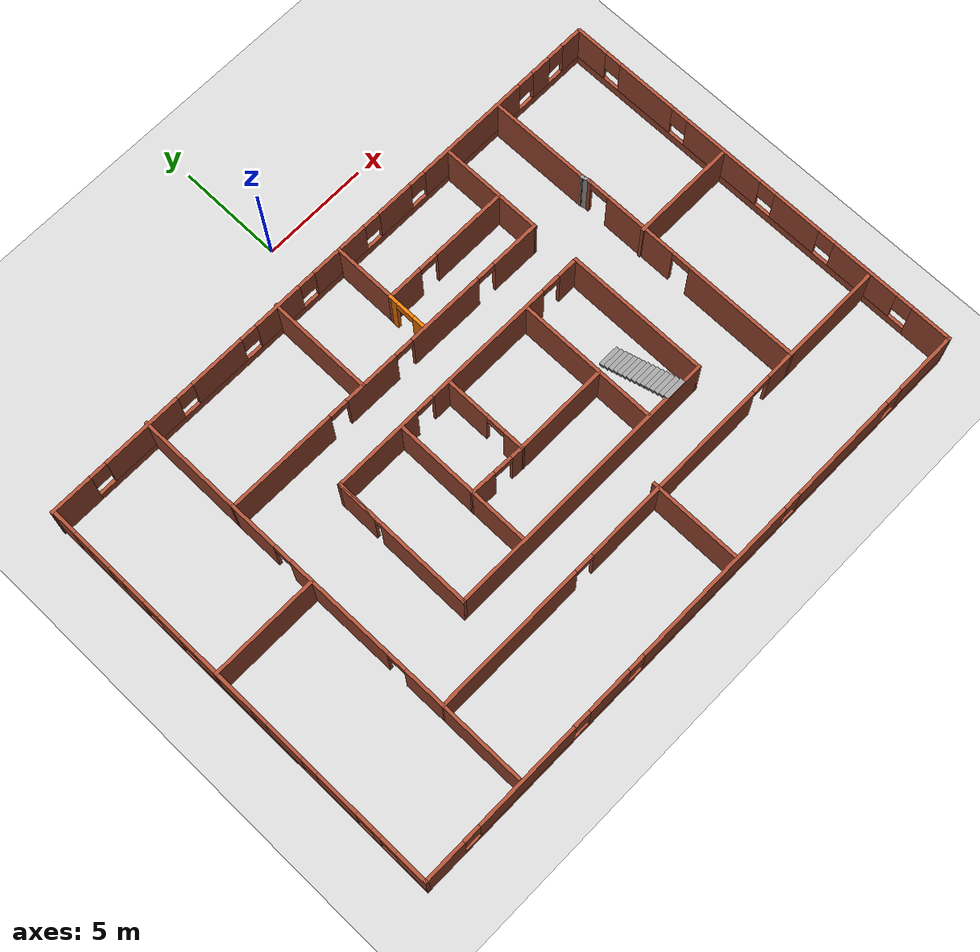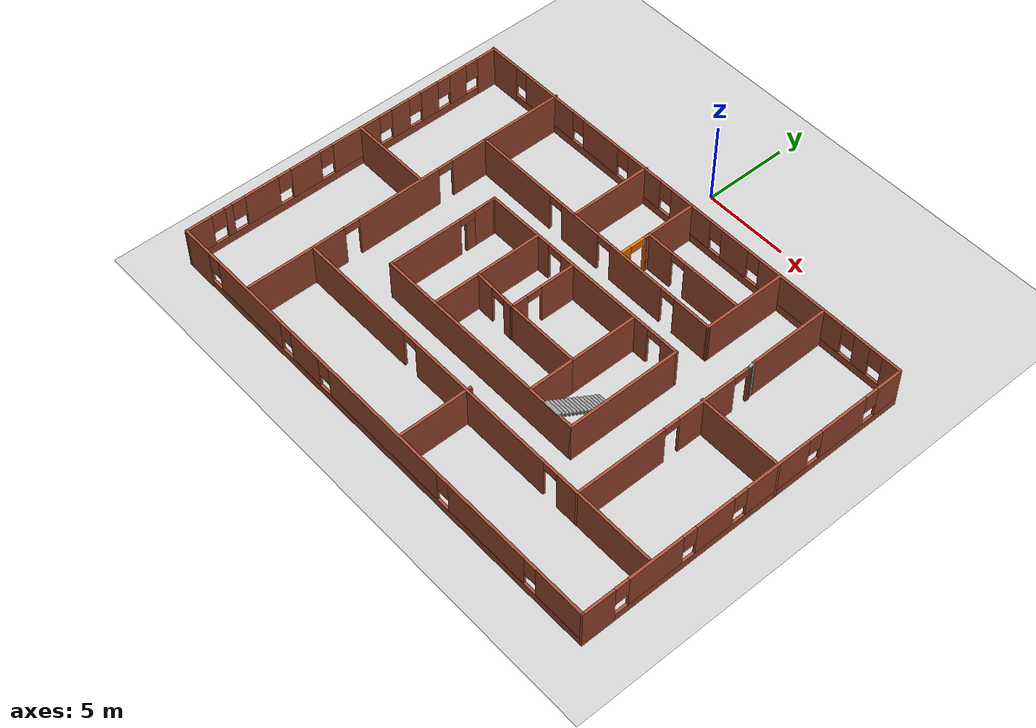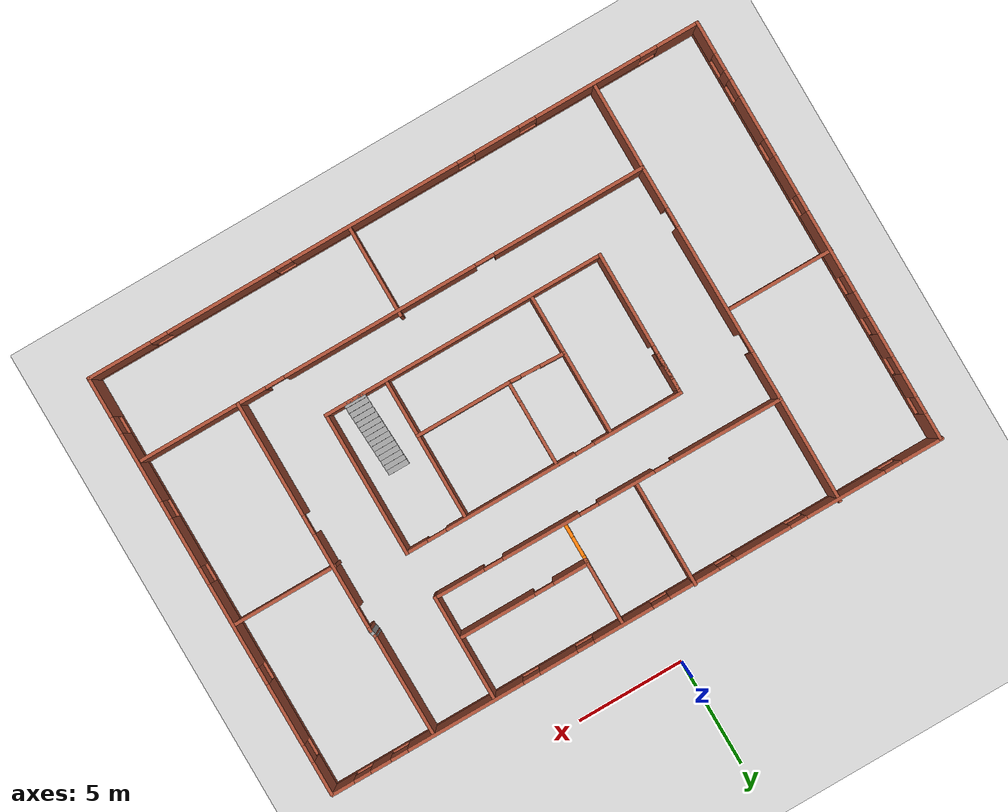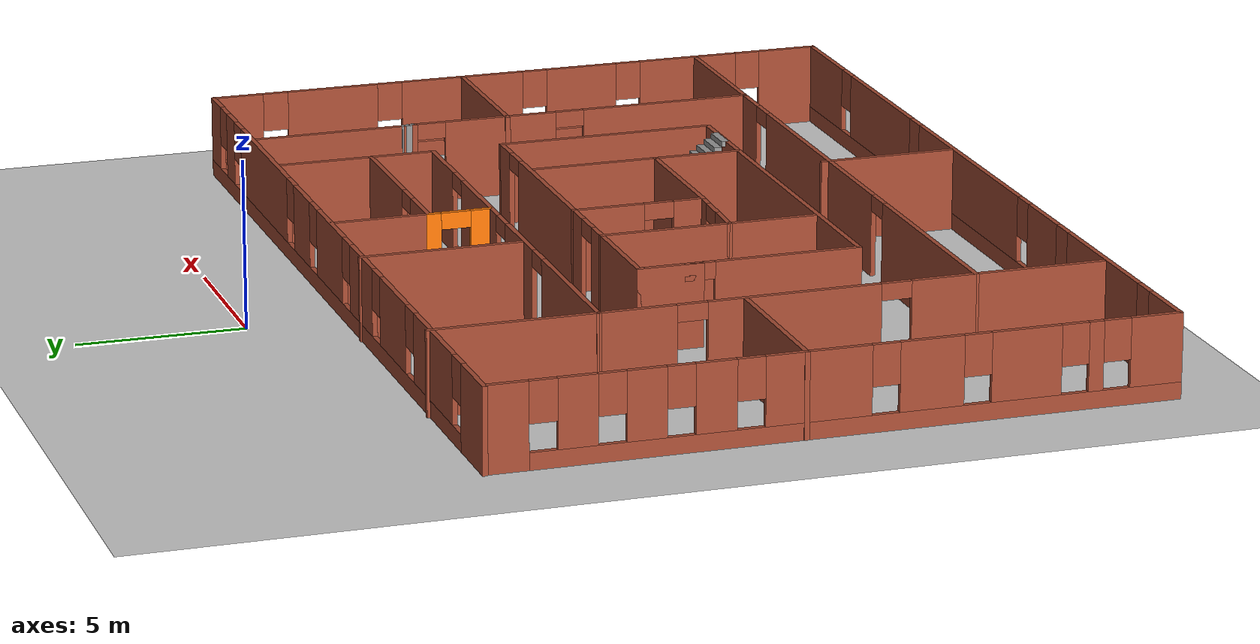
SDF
<sdf version="1.7">
 <world name="default">
  <light name="sun" type="directional">
   <pose>0 0 10 0 -0 0</pose>
   <diffuse>0.8 0.8 0.8 1</diffuse>
   <specular>0.2 0.2 0.2 1</specular>
   <attenuation>
    <range>1000</range>
    <constant>0.9</constant>
    <linear>0.01</linear>
    <quadratic>0.001</quadratic>
   </attenuation>
   <direction>-0.5 0.1 -0.9</direction>
   <spot><inner_angle>0</inner_angle><outer_angle>0</outer_angle><falloff>0</falloff></spot>
  </light>
  <model name="ground_plane">
   <static>1</static>
   <link name="link">
    <collision name="collision">
     <geometry><plane><normal>0 0 1</normal><size>100 100</size></plane></geometry>
     <surface>
      <contact><collide_bitmask>65535</collide_bitmask></contact>
      <friction><ode><mu>100</mu><mu2>50</mu2></ode></friction>
     </surface>
    </collision>
    <visual name="visual">
     <cast_shadows>0</cast_shadows>
     <geometry><plane><normal>0 0 1</normal><size>100 100</size></plane></geometry>
     <material>
      <script><uri>file://media/materials/scripts/gazebo.material</uri><name>Gazebo/Grey</name></script>
     </material>
    </visual>
   </link>
  </model>
  <gravity>0 0 -9.8</gravity>
  <magnetic_field>6e-06 2.3e-05 -4.2e-05</magnetic_field>
  <atmosphere type="adiabatic"/>
  <physics type="ode">
   <max_step_size>0.001</max_step_size>
   <real_time_factor>1</real_time_factor>
   <real_time_update_rate>1000</real_time_update_rate>
  </physics>
  <scene><ambient>0.4 0.4 0.4 1</ambient><background>0.7 0.7 0.7 1</background><shadows>1</shadows></scene>
  <audio><device>default</device></audio>
  <spherical_coordinates>
   <surface_model>EARTH_WGS84</surface_model>
   <latitude_deg>0</latitude_deg>
   <longitude_deg>0</longitude_deg>
   <elevation>0</elevation>
   <heading_deg>0</heading_deg>
  </spherical_coordinates>
  <model name="dh-hdh">
   <pose>0.666955 -11.441 0 0 -0 0</pose>
   <link name="Stairs_3">
    <visual name="Stairs_3_Visual_0">
     <pose>5.54539 -1.78177 0.083333 0 -0 0</pose>
     <geometry><box><size>1 0.233333 0.166667</size></box></geometry>
     <material>
      <script><uri>file://media/materials/scripts/gazebo.material</uri><name>Gazebo/Grey</name></script>
      <ambient>1 1 1 1</ambient>
     </material>
     <meta><layer>0</layer></meta>
    </visual>
    <collision name="Stairs_3_Collision_0">
     <geometry><box><size>1 0.233333 0.166667</size></box></geometry>
     <pose>5.54539 -1.78177 0.083333 0 -0 0</pose>
    </collision>
    <visual name="Stairs_3_Visual_1">
     <pose>5.54539 -2.0151 0.25 0 -0 0</pose>
     <geometry><box><size>1 0.233333 0.166667</size></box></geometry>
     <material>
      <script><uri>file://media/materials/scripts/gazebo.material</uri><name>Gazebo/Grey</name></script>
      <ambient>1 1 1 1</ambient>
     </material>
     <meta><layer>0</layer></meta>
    </visual>
    <collision name="Stairs_3_Collision_1">
     <geometry><box><size>1 0.233333 0.166667</size></box></geometry>
     <pose>5.54539 -2.0151 0.25 0 -0 0</pose>
    </collision>
    <visual name="Stairs_3_Visual_2">
     <pose>5.54539 -2.24844 0.416667 0 -0 0</pose>
     <geometry><box><size>1 0.233333 0.166667</size></box></geometry>
     <material>
      <script><uri>file://media/materials/scripts/gazebo.material</uri><name>Gazebo/Grey</name></script>
      <ambient>1 1 1 1</ambient>
     </material>
     <meta><layer>0</layer></meta>
    </visual>
    <collision name="Stairs_3_Collision_2">
     <geometry><box><size>1 0.233333 0.166667</size></box></geometry>
     <pose>5.54539 -2.24844 0.416667 0 -0 0</pose>
    </collision>
    <visual name="Stairs_3_Visual_3">
     <pose>5.54539 -2.48177 0.583333 0 -0 0</pose>
     <geometry><box><size>1 0.233333 0.166667</size></box></geometry>
     <material>
      <script><uri>file://media/materials/scripts/gazebo.material</uri><name>Gazebo/Grey</name></script>
      <ambient>1 1 1 1</ambient>
     </material>
     <meta><layer>0</layer></meta>
    </visual>
    <collision name="Stairs_3_Collision_3">
     <geometry><box><size>1 0.233333 0.166667</size></box></geometry>
     <pose>5.54539 -2.48177 0.583333 0 -0 0</pose>
    </collision>
    <visual name="Stairs_3_Visual_4">
     <pose>5.54539 -2.7151 0.75 0 -0 0</pose>
     <geometry><box><size>1 0.233333 0.166667</size></box></geometry>
     <material>
      <script><uri>file://media/materials/scripts/gazebo.material</uri><name>Gazebo/Grey</name></script>
      <ambient>1 1 1 1</ambient>
     </material>
     <meta><layer>0</layer></meta>
    </visual>
    <collision name="Stairs_3_Collision_4">
     <geometry><box><size>1 0.233333 0.166667</size></box></geometry>
     <pose>5.54539 -2.7151 0.75 0 -0 0</pose>
    </collision>
    <visual name="Stairs_3_Visual_5">
     <pose>5.54539 -2.94843 0.916667 0 -0 0</pose>
     <geometry><box><size>1 0.233333 0.166667</size></box></geometry>
     <material>
      <script><uri>file://media/materials/scripts/gazebo.material</uri><name>Gazebo/Grey</name></script>
      <ambient>1 1 1 1</ambient>
     </material>
     <meta><layer>0</layer></meta>
    </visual>
    <collision name="Stairs_3_Collision_5">
     <geometry><box><size>1 0.233333 0.166667</size></box></geometry>
     <pose>5.54539 -2.94843 0.916667 0 -0 0</pose>
    </collision>
    <visual name="Stairs_3_Visual_6">
     <pose>5.54539 -3.18177 1.08333 0 -0 0</pose>
     <geometry><box><size>1 0.233333 0.166667</size></box></geometry>
     <material>
      <script><uri>file://media/materials/scripts/gazebo.material</uri><name>Gazebo/Grey</name></script>
      <ambient>1 1 1 1</ambient>
     </material>
     <meta><layer>0</layer></meta>
    </visual>
    <collision name="Stairs_3_Collision_6">
     <geometry><box><size>1 0.233333 0.166667</size></box></geometry>
     <pose>5.54539 -3.18177 1.08333 0 -0 0</pose>
    </collision>
    <visual name="Stairs_3_Visual_7">
     <pose>5.54539 -3.4151 1.25 0 -0 0</pose>
     <geometry><box><size>1 0.233333 0.166667</size></box></geometry>
     <material>
      <script><uri>file://media/materials/scripts/gazebo.material</uri><name>Gazebo/Grey</name></script>
      <ambient>1 1 1 1</ambient>
     </material>
     <meta><layer>0</layer></meta>
    </visual>
    <collision name="Stairs_3_Collision_7">
     <geometry><box><size>1 0.233333 0.166667</size></box></geometry>
     <pose>5.54539 -3.4151 1.25 0 -0 0</pose>
    </collision>
    <visual name="Stairs_3_Visual_8">
     <pose>5.54539 -3.64844 1.41667 0 -0 0</pose>
     <geometry><box><size>1 0.233333 0.166667</size></box></geometry>
     <material>
      <script><uri>file://media/materials/scripts/gazebo.material</uri><name>Gazebo/Grey</name></script>
      <ambient>1 1 1 1</ambient>
     </material>
     <meta><layer>0</layer></meta>
    </visual>
    <collision name="Stairs_3_Collision_8">
     <geometry><box><size>1 0.233333 0.166667</size></box></geometry>
     <pose>5.54539 -3.64844 1.41667 0 -0 0</pose>
    </collision>
    <visual name="Stairs_3_Visual_9">
     <pose>5.54539 -3.88177 1.58333 0 -0 0</pose>
     <geometry><box><size>1 0.233333 0.166667</size></box></geometry>
     <material>
      <script><uri>file://media/materials/scripts/gazebo.material</uri><name>Gazebo/Grey</name></script>
      <ambient>1 1 1 1</ambient>
     </material>
     <meta><layer>0</layer></meta>
    </visual>
    <collision name="Stairs_3_Collision_9">
     <geometry><box><size>1 0.233333 0.166667</size></box></geometry>
     <pose>5.54539 -3.88177 1.58333 0 -0 0</pose>
    </collision>
    <visual name="Stairs_3_Visual_10">
     <pose>5.54539 -4.1151 1.75 0 -0 0</pose>
     <geometry><box><size>1 0.233333 0.166667</size></box></geometry>
     <material>
      <script><uri>file://media/materials/scripts/gazebo.material</uri><name>Gazebo/Grey</name></script>
      <ambient>1 1 1 1</ambient>
     </material>
     <meta><layer>0</layer></meta>
    </visual>
    <collision name="Stairs_3_Collision_10">
     <geometry><box><size>1 0.233333 0.166667</size></box></geometry>
     <pose>5.54539 -4.1151 1.75 0 -0 0</pose>
    </collision>
    <visual name="Stairs_3_Visual_11">
     <pose>5.54539 -4.34844 1.91667 0 -0 0</pose>
     <geometry><box><size>1 0.233333 0.166667</size></box></geometry>
     <material>
      <script><uri>file://media/materials/scripts/gazebo.material</uri><name>Gazebo/Grey</name></script>
      <ambient>1 1 1 1</ambient>
     </material>
     <meta><layer>0</layer></meta>
    </visual>
    <collision name="Stairs_3_Collision_11">
     <geometry><box><size>1 0.233333 0.166667</size></box></geometry>
     <pose>5.54539 -4.34844 1.91667 0 -0 0</pose>
    </collision>
    <visual name="Stairs_3_Visual_12">
     <pose>5.54539 -4.58177 2.08333 0 -0 0</pose>
     <geometry><box><size>1 0.233333 0.166667</size></box></geometry>
     <material>
      <script><uri>file://media/materials/scripts/gazebo.material</uri><name>Gazebo/Grey</name></script>
      <ambient>1 1 1 1</ambient>
     </material>
     <meta><layer>0</layer></meta>
    </visual>
    <collision name="Stairs_3_Collision_12">
     <geometry><box><size>1 0.233333 0.166667</size></box></geometry>
     <pose>5.54539 -4.58177 2.08333 0 -0 0</pose>
    </collision>
    <visual name="Stairs_3_Visual_13">
     <pose>5.54539 -4.8151 2.25 0 -0 0</pose>
     <geometry><box><size>1 0.233333 0.166667</size></box></geometry>
     <material>
      <script><uri>file://media/materials/scripts/gazebo.material</uri><name>Gazebo/Grey</name></script>
      <ambient>1 1 1 1</ambient>
     </material>
     <meta><layer>0</layer></meta>
    </visual>
    <collision name="Stairs_3_Collision_13">
     <geometry><box><size>1 0.233333 0.166667</size></box></geometry>
     <pose>5.54539 -4.8151 2.25 0 -0 0</pose>
    </collision>
    <visual name="Stairs_3_Visual_14">
     <pose>5.54539 -5.04843 2.41667 0 -0 0</pose>
     <geometry><box><size>1 0.233333 0.166667</size></box></geometry>
     <material>
      <script><uri>file://media/materials/scripts/gazebo.material</uri><name>Gazebo/Grey</name></script>
      <ambient>1 1 1 1</ambient>
     </material>
     <meta><layer>0</layer></meta>
    </visual>
    <collision name="Stairs_3_Collision_14">
     <geometry><box><size>1 0.233333 0.166667</size></box></geometry>
     <pose>5.54539 -5.04843 2.41667 0 -0 0</pose>
    </collision>
   </link>
   <link name="Wall_26">
    <pose>-14.5246 -1.44103 0 0 -0 -1.5708</pose>
    <visual name="Wall_26_Visual_0">
     <pose>-9.37751 0 1.25 0 -0 0</pose>
     <geometry><box><size>1.24497 0.15 2.5</size></box></geometry>
     <material>
      <script><uri>file://media/materials/scripts/gazebo.material</uri><name>Gazebo/Bricks</name></script>
      <ambient>0.466667 0.462745 0.482353 1</ambient>
     </material>
     <meta><layer>0</layer></meta>
    </visual>
    <collision name="Wall_26_Collision_0">
     <geometry><box><size>1.24497 0.15 2.5</size></box></geometry>
     <pose>-9.37751 0 1.25 0 -0 0</pose>
    </collision>
    <visual name="Wall_26_Visual_1">
     <pose>0.622486 0 0.25 0 -0 0</pose>
     <geometry><box><size>18.755 0.15 0.5</size></box></geometry>
     <material>
      <script><uri>file://media/materials/scripts/gazebo.material</uri><name>Gazebo/Bricks</name></script>
      <ambient>0.466667 0.462745 0.482353 1</ambient>
     </material>
     <meta><layer>0</layer></meta>
    </visual>
    <collision name="Wall_26_Collision_1">
     <geometry><box><size>18.755 0.15 0.5</size></box></geometry>
     <pose>0.622486 0 0.25 0 -0 0</pose>
    </collision>
    <visual name="Wall_26_Visual_2">
     <pose>-7.39044 0 1.5 0 -0 0</pose>
     <geometry><box><size>1.12917 0.15 2</size></box></geometry>
     <material>
      <script><uri>file://media/materials/scripts/gazebo.material</uri><name>Gazebo/Bricks</name></script>
      <ambient>0.466667 0.462745 0.482353 1</ambient>
     </material>
     <meta><layer>0</layer></meta>
    </visual>
    <collision name="Wall_26_Collision_2">
     <geometry><box><size>1.12917 0.15 2</size></box></geometry>
     <pose>-7.39044 0 1.5 0 -0 0</pose>
    </collision>
    <visual name="Wall_26_Visual_3">
     <pose>-5.46128 0 1.5 0 -0 0</pose>
     <geometry><box><size>1.12917 0.15 2</size></box></geometry>
     <material>
      <script><uri>file://media/materials/scripts/gazebo.material</uri><name>Gazebo/Bricks</name></script>
      <ambient>0.466667 0.462745 0.482353 1</ambient>
     </material>
     <meta><layer>0</layer></meta>
    </visual>
    <collision name="Wall_26_Collision_3">
     <geometry><box><size>1.12917 0.15 2</size></box></geometry>
     <pose>-5.46128 0 1.5 0 -0 0</pose>
    </collision>
    <visual name="Wall_26_Visual_4">
     <pose>-3.51159 0 1.5 0 -0 0</pose>
     <geometry><box><size>1.17021 0.15 2</size></box></geometry>
     <material>
      <script><uri>file://media/materials/scripts/gazebo.material</uri><name>Gazebo/Bricks</name></script>
      <ambient>0.466667 0.462745 0.482353 1</ambient>
     </material>
     <meta><layer>0</layer></meta>
    </visual>
    <collision name="Wall_26_Collision_4">
     <geometry><box><size>1.17021 0.15 2</size></box></geometry>
     <pose>-3.51159 0 1.5 0 -0 0</pose>
    </collision>
    <visual name="Wall_26_Visual_5">
     <pose>-0.603063 0 1.5 0 -0 0</pose>
     <geometry><box><size>3.04683 0.15 2</size></box></geometry>
     <material>
      <script><uri>file://media/materials/scripts/gazebo.material</uri><name>Gazebo/Bricks</name></script>
      <ambient>0.466667 0.462745 0.482353 1</ambient>
     </material>
     <meta><layer>0</layer></meta>
    </visual>
    <collision name="Wall_26_Collision_5">
     <geometry><box><size>3.04683 0.15 2</size></box></geometry>
     <pose>-0.603063 0 1.5 0 -0 0</pose>
    </collision>
    <visual name="Wall_26_Visual_6">
     <pose>2.64954 0 1.5 0 -0 0</pose>
     <geometry><box><size>1.85838 0.15 2</size></box></geometry>
     <material>
      <script><uri>file://media/materials/scripts/gazebo.material</uri><name>Gazebo/Bricks</name></script>
      <ambient>0.466667 0.462745 0.482353 1</ambient>
     </material>
     <meta><layer>0</layer></meta>
    </visual>
    <collision name="Wall_26_Collision_6">
     <geometry><box><size>1.85838 0.15 2</size></box></geometry>
     <pose>2.64954 0 1.5 0 -0 0</pose>
    </collision>
    <visual name="Wall_26_Visual_7">
     <pose>5.40287 0 1.5 0 -0 0</pose>
     <geometry><box><size>2.04827 0.15 2</size></box></geometry>
     <material>
      <script><uri>file://media/materials/scripts/gazebo.material</uri><name>Gazebo/Bricks</name></script>
      <ambient>0.466667 0.462745 0.482353 1</ambient>
     </material>
     <meta><layer>0</layer></meta>
    </visual>
    <collision name="Wall_26_Collision_7">
     <geometry><box><size>2.04827 0.15 2</size></box></geometry>
     <pose>5.40287 0 1.5 0 -0 0</pose>
    </collision>
    <visual name="Wall_26_Visual_8">
     <pose>7.44412 0 1.5 0 -0 0</pose>
     <geometry><box><size>0.434249 0.15 2</size></box></geometry>
     <material>
      <script><uri>file://media/materials/scripts/gazebo.material</uri><name>Gazebo/Bricks</name></script>
      <ambient>0.466667 0.462745 0.482353 1</ambient>
     </material>
     <meta><layer>0</layer></meta>
    </visual>
    <collision name="Wall_26_Collision_8">
     <geometry><box><size>0.434249 0.15 2</size></box></geometry>
     <pose>7.44412 0 1.5 0 -0 0</pose>
    </collision>
    <visual name="Wall_26_Visual_9">
     <pose>9.23062 0 1.5 0 -0 0</pose>
     <geometry><box><size>1.53875 0.15 2</size></box></geometry>
     <material>
      <script><uri>file://media/materials/scripts/gazebo.material</uri><name>Gazebo/Bricks</name></script>
      <ambient>0.466667 0.462745 0.482353 1</ambient>
     </material>
     <meta><layer>0</layer></meta>
    </visual>
    <collision name="Wall_26_Collision_9">
     <geometry><box><size>1.53875 0.15 2</size></box></geometry>
     <pose>9.23062 0 1.5 0 -0 0</pose>
    </collision>
    <visual name="Wall_26_Visual_10">
     <pose>-8.35503 0 1.9 0 -0 0</pose>
     <geometry><box><size>0.8 0.15 1.2</size></box></geometry>
     <material>
      <script><uri>file://media/materials/scripts/gazebo.material</uri><name>Gazebo/Bricks</name></script>
      <ambient>0.466667 0.462745 0.482353 1</ambient>
     </material>
     <meta><layer>0</layer></meta>
    </visual>
    <collision name="Wall_26_Collision_10">
     <geometry><box><size>0.8 0.15 1.2</size></box></geometry>
     <pose>-8.35503 0 1.9 0 -0 0</pose>
    </collision>
    <visual name="Wall_26_Visual_11">
     <pose>-6.42586 0 1.9 0 -0 0</pose>
     <geometry><box><size>0.8 0.15 1.2</size></box></geometry>
     <material>
      <script><uri>file://media/materials/scripts/gazebo.material</uri><name>Gazebo/Bricks</name></script>
      <ambient>0.466667 0.462745 0.482353 1</ambient>
     </material>
     <meta><layer>0</layer></meta>
    </visual>
    <collision name="Wall_26_Collision_11">
     <geometry><box><size>0.8 0.15 1.2</size></box></geometry>
     <pose>-6.42586 0 1.9 0 -0 0</pose>
    </collision>
    <visual name="Wall_26_Visual_12">
     <pose>-4.49669 0 1.9 0 -0 0</pose>
     <geometry><box><size>0.8 0.15 1.2</size></box></geometry>
     <material>
      <script><uri>file://media/materials/scripts/gazebo.material</uri><name>Gazebo/Bricks</name></script>
      <ambient>0.466667 0.462745 0.482353 1</ambient>
     </material>
     <meta><layer>0</layer></meta>
    </visual>
    <collision name="Wall_26_Collision_12">
     <geometry><box><size>0.8 0.15 1.2</size></box></geometry>
     <pose>-4.49669 0 1.9 0 -0 0</pose>
    </collision>
    <visual name="Wall_26_Visual_13">
     <pose>-2.52648 0 1.9 0 -0 0</pose>
     <geometry><box><size>0.8 0.15 1.2</size></box></geometry>
     <material>
      <script><uri>file://media/materials/scripts/gazebo.material</uri><name>Gazebo/Bricks</name></script>
      <ambient>0.466667 0.462745 0.482353 1</ambient>
     </material>
     <meta><layer>0</layer></meta>
    </visual>
    <collision name="Wall_26_Collision_13">
     <geometry><box><size>0.8 0.15 1.2</size></box></geometry>
     <pose>-2.52648 0 1.9 0 -0 0</pose>
    </collision>
    <visual name="Wall_26_Visual_14">
     <pose>1.32035 0 1.9 0 -0 0</pose>
     <geometry><box><size>0.8 0.15 1.2</size></box></geometry>
     <material>
      <script><uri>file://media/materials/scripts/gazebo.material</uri><name>Gazebo/Bricks</name></script>
      <ambient>0.466667 0.462745 0.482353 1</ambient>
     </material>
     <meta><layer>0</layer></meta>
    </visual>
    <collision name="Wall_26_Collision_14">
     <geometry><box><size>0.8 0.15 1.2</size></box></geometry>
     <pose>1.32035 0 1.9 0 -0 0</pose>
    </collision>
    <visual name="Wall_26_Visual_15">
     <pose>3.97873 0 1.9 0 -0 0</pose>
     <geometry><box><size>0.8 0.15 1.2</size></box></geometry>
     <material>
      <script><uri>file://media/materials/scripts/gazebo.material</uri><name>Gazebo/Bricks</name></script>
      <ambient>0.466667 0.462745 0.482353 1</ambient>
     </material>
     <meta><layer>0</layer></meta>
    </visual>
    <collision name="Wall_26_Collision_15">
     <geometry><box><size>0.8 0.15 1.2</size></box></geometry>
     <pose>3.97873 0 1.9 0 -0 0</pose>
    </collision>
    <visual name="Wall_26_Visual_16">
     <pose>6.827 0 1.9 0 -0 0</pose>
     <geometry><box><size>0.8 0.15 1.2</size></box></geometry>
     <material>
      <script><uri>file://media/materials/scripts/gazebo.material</uri><name>Gazebo/Bricks</name></script>
      <ambient>0.466667 0.462745 0.482353 1</ambient>
     </material>
     <meta><layer>0</layer></meta>
    </visual>
    <collision name="Wall_26_Collision_16">
     <geometry><box><size>0.8 0.15 1.2</size></box></geometry>
     <pose>6.827 0 1.9 0 -0 0</pose>
    </collision>
    <visual name="Wall_26_Visual_17">
     <pose>8.06125 0 1.9 0 -0 0</pose>
     <geometry><box><size>0.8 0.15 1.2</size></box></geometry>
     <material>
      <script><uri>file://media/materials/scripts/gazebo.material</uri><name>Gazebo/Bricks</name></script>
      <ambient>0.466667 0.462745 0.482353 1</ambient>
     </material>
     <meta><layer>0</layer></meta>
    </visual>
    <collision name="Wall_26_Collision_17">
     <geometry><box><size>0.8 0.15 1.2</size></box></geometry>
     <pose>8.06125 0 1.9 0 -0 0</pose>
    </collision>
   </link>
   <link name="Wall_27">
    <pose>0.025415 -11.366 0 0 -0 0</pose>
    <visual name="Wall_27_Visual_0">
     <pose>-13.6119 0 1.25 0 -0 0</pose>
     <geometry><box><size>2.02613 0.15 2.5</size></box></geometry>
     <material>
      <script><uri>file://media/materials/scripts/gazebo.material</uri><name>Gazebo/Bricks</name></script>
      <ambient>0.466667 0.462745 0.482353 1</ambient>
     </material>
     <meta><layer>0</layer></meta>
    </visual>
    <collision name="Wall_27_Collision_0">
     <geometry><box><size>2.02613 0.15 2.5</size></box></geometry>
     <pose>-13.6119 0 1.25 0 -0 0</pose>
    </collision>
    <visual name="Wall_27_Visual_1">
     <pose>1.01306 0 0.25 0 -0 0</pose>
     <geometry><box><size>27.2239 0.15 0.5</size></box></geometry>
     <material>
      <script><uri>file://media/materials/scripts/gazebo.material</uri><name>Gazebo/Bricks</name></script>
      <ambient>0.466667 0.462745 0.482353 1</ambient>
     </material>
     <meta><layer>0</layer></meta>
    </visual>
    <collision name="Wall_27_Collision_1">
     <geometry><box><size>27.2239 0.15 0.5</size></box></geometry>
     <pose>1.01306 0 0.25 0 -0 0</pose>
    </collision>
    <visual name="Wall_27_Visual_2">
     <pose>-9.30313 0 1.5 0 -0 0</pose>
     <geometry><box><size>4.99147 0.15 2</size></box></geometry>
     <material>
      <script><uri>file://media/materials/scripts/gazebo.material</uri><name>Gazebo/Bricks</name></script>
      <ambient>0.466667 0.462745 0.482353 1</ambient>
     </material>
     <meta><layer>0</layer></meta>
    </visual>
    <collision name="Wall_27_Collision_2">
     <geometry><box><size>4.99147 0.15 2</size></box></geometry>
     <pose>-9.30313 0 1.5 0 -0 0</pose>
    </collision>
    <visual name="Wall_27_Visual_3">
     <pose>-4.93579 0 1.5 0 -0 0</pose>
     <geometry><box><size>2.14321 0.15 2</size></box></geometry>
     <material>
      <script><uri>file://media/materials/scripts/gazebo.material</uri><name>Gazebo/Bricks</name></script>
      <ambient>0.466667 0.462745 0.482353 1</ambient>
     </material>
     <meta><layer>0</layer></meta>
    </visual>
    <collision name="Wall_27_Collision_3">
     <geometry><box><size>2.14321 0.15 2</size></box></geometry>
     <pose>-4.93579 0 1.5 0 -0 0</pose>
    </collision>
    <visual name="Wall_27_Visual_4">
     <pose>0.896215 0 1.5 0 -0 0</pose>
     <geometry><box><size>7.92081 0.15 2</size></box></geometry>
     <material>
      <script><uri>file://media/materials/scripts/gazebo.material</uri><name>Gazebo/Bricks</name></script>
      <ambient>0.466667 0.462745 0.482353 1</ambient>
     </material>
     <meta><layer>0</layer></meta>
    </visual>
    <collision name="Wall_27_Collision_4">
     <geometry><box><size>7.92081 0.15 2</size></box></geometry>
     <pose>0.896215 0 1.5 0 -0 0</pose>
    </collision>
    <visual name="Wall_27_Visual_5">
     <pose>8.22872 0 1.5 0 -0 0</pose>
     <geometry><box><size>5.14421 0.15 2</size></box></geometry>
     <material>
      <script><uri>file://media/materials/scripts/gazebo.material</uri><name>Gazebo/Bricks</name></script>
      <ambient>0.466667 0.462745 0.482353 1</ambient>
     </material>
     <meta><layer>0</layer></meta>
    </visual>
    <collision name="Wall_27_Collision_5">
     <geometry><box><size>5.14421 0.15 2</size></box></geometry>
     <pose>8.22872 0 1.5 0 -0 0</pose>
    </collision>
    <visual name="Wall_27_Visual_6">
     <pose>13.1129 0 1.5 0 -0 0</pose>
     <geometry><box><size>3.02417 0.15 2</size></box></geometry>
     <material>
      <script><uri>file://media/materials/scripts/gazebo.material</uri><name>Gazebo/Bricks</name></script>
      <ambient>0.466667 0.462745 0.482353 1</ambient>
     </material>
     <meta><layer>0</layer></meta>
    </visual>
    <collision name="Wall_27_Collision_6">
     <geometry><box><size>3.02417 0.15 2</size></box></geometry>
     <pose>13.1129 0 1.5 0 -0 0</pose>
    </collision>
    <visual name="Wall_27_Visual_7">
     <pose>-12.1989 0 1.9 0 -0 0</pose>
     <geometry><box><size>0.8 0.15 1.2</size></box></geometry>
     <material>
      <script><uri>file://media/materials/scripts/gazebo.material</uri><name>Gazebo/Bricks</name></script>
      <ambient>0.466667 0.462745 0.482353 1</ambient>
     </material>
     <meta><layer>0</layer></meta>
    </visual>
    <collision name="Wall_27_Collision_7">
     <geometry><box><size>0.8 0.15 1.2</size></box></geometry>
     <pose>-12.1989 0 1.9 0 -0 0</pose>
    </collision>
    <visual name="Wall_27_Visual_8">
     <pose>-6.4074 0 1.9 0 -0 0</pose>
     <geometry><box><size>0.8 0.15 1.2</size></box></geometry>
     <material>
      <script><uri>file://media/materials/scripts/gazebo.material</uri><name>Gazebo/Bricks</name></script>
      <ambient>0.466667 0.462745 0.482353 1</ambient>
     </material>
     <meta><layer>0</layer></meta>
    </visual>
    <collision name="Wall_27_Collision_8">
     <geometry><box><size>0.8 0.15 1.2</size></box></geometry>
     <pose>-6.4074 0 1.9 0 -0 0</pose>
    </collision>
    <visual name="Wall_27_Visual_9">
     <pose>-3.46419 0 1.9 0 -0 0</pose>
     <geometry><box><size>0.8 0.15 1.2</size></box></geometry>
     <material>
      <script><uri>file://media/materials/scripts/gazebo.material</uri><name>Gazebo/Bricks</name></script>
      <ambient>0.466667 0.462745 0.482353 1</ambient>
     </material>
     <meta><layer>0</layer></meta>
    </visual>
    <collision name="Wall_27_Collision_9">
     <geometry><box><size>0.8 0.15 1.2</size></box></geometry>
     <pose>-3.46419 0 1.9 0 -0 0</pose>
    </collision>
    <visual name="Wall_27_Visual_10">
     <pose>5.25662 0 1.9 0 -0 0</pose>
     <geometry><box><size>0.8 0.15 1.2</size></box></geometry>
     <material>
      <script><uri>file://media/materials/scripts/gazebo.material</uri><name>Gazebo/Bricks</name></script>
      <ambient>0.466667 0.462745 0.482353 1</ambient>
     </material>
     <meta><layer>0</layer></meta>
    </visual>
    <collision name="Wall_27_Collision_10">
     <geometry><box><size>0.8 0.15 1.2</size></box></geometry>
     <pose>5.25662 0 1.9 0 -0 0</pose>
    </collision>
    <visual name="Wall_27_Visual_11">
     <pose>11.2008 0 1.9 0 -0 0</pose>
     <geometry><box><size>0.8 0.15 1.2</size></box></geometry>
     <material>
      <script><uri>file://media/materials/scripts/gazebo.material</uri><name>Gazebo/Bricks</name></script>
      <ambient>0.466667 0.462745 0.482353 1</ambient>
     </material>
     <meta><layer>0</layer></meta>
    </visual>
    <collision name="Wall_27_Collision_11">
     <geometry><box><size>0.8 0.15 1.2</size></box></geometry>
     <pose>11.2008 0 1.9 0 -0 0</pose>
    </collision>
   </link>
   <link name="Wall_28">
    <pose>14.5754 -1.44103 0 0 -0 1.5708</pose>
    <visual name="Wall_28_Visual_0">
     <pose>-9.03458 0 1.25 0 -0 0</pose>
     <geometry><box><size>1.93084 0.15 2.5</size></box></geometry>
     <material>
      <script><uri>file://media/materials/scripts/gazebo.material</uri><name>Gazebo/Bricks</name></script>
      <ambient>0.466667 0.462745 0.482353 1</ambient>
     </material>
     <meta><layer>0</layer></meta>
    </visual>
    <collision name="Wall_28_Collision_0">
     <geometry><box><size>1.93084 0.15 2.5</size></box></geometry>
     <pose>-9.03458 0 1.25 0 -0 0</pose>
    </collision>
    <visual name="Wall_28_Visual_1">
     <pose>0.965422 0 0.25 0 -0 0</pose>
     <geometry><box><size>18.0692 0.15 0.5</size></box></geometry>
     <material>
      <script><uri>file://media/materials/scripts/gazebo.material</uri><name>Gazebo/Bricks</name></script>
      <ambient>0.466667 0.462745 0.482353 1</ambient>
     </material>
     <meta><layer>0</layer></meta>
    </visual>
    <collision name="Wall_28_Collision_1">
     <geometry><box><size>18.0692 0.15 0.5</size></box></geometry>
     <pose>0.965422 0 0.25 0 -0 0</pose>
    </collision>
    <visual name="Wall_28_Visual_2">
     <pose>-5.64647 0 1.5 0 -0 0</pose>
     <geometry><box><size>3.24536 0.15 2</size></box></geometry>
     <material>
      <script><uri>file://media/materials/scripts/gazebo.material</uri><name>Gazebo/Bricks</name></script>
      <ambient>0.466667 0.462745 0.482353 1</ambient>
     </material>
     <meta><layer>0</layer></meta>
    </visual>
    <collision name="Wall_28_Collision_2">
     <geometry><box><size>3.24536 0.15 2</size></box></geometry>
     <pose>-5.64647 0 1.5 0 -0 0</pose>
    </collision>
    <visual name="Wall_28_Visual_3">
     <pose>-2.05518 0 1.5 0 -0 0</pose>
     <geometry><box><size>2.33722 0.15 2</size></box></geometry>
     <material>
      <script><uri>file://media/materials/scripts/gazebo.material</uri><name>Gazebo/Bricks</name></script>
      <ambient>0.466667 0.462745 0.482353 1</ambient>
     </material>
     <meta><layer>0</layer></meta>
    </visual>
    <collision name="Wall_28_Collision_3">
     <geometry><box><size>2.33722 0.15 2</size></box></geometry>
     <pose>-2.05518 0 1.5 0 -0 0</pose>
    </collision>
    <visual name="Wall_28_Visual_4">
     <pose>1.90762 0 1.5 0 -0 0</pose>
     <geometry><box><size>3.98839 0.15 2</size></box></geometry>
     <material>
      <script><uri>file://media/materials/scripts/gazebo.material</uri><name>Gazebo/Bricks</name></script>
      <ambient>0.466667 0.462745 0.482353 1</ambient>
     </material>
     <meta><layer>0</layer></meta>
    </visual>
    <collision name="Wall_28_Collision_4">
     <geometry><box><size>3.98839 0.15 2</size></box></geometry>
     <pose>1.90762 0 1.5 0 -0 0</pose>
    </collision>
    <visual name="Wall_28_Visual_5">
     <pose>6.15938 0 1.5 0 -0 0</pose>
     <geometry><box><size>2.91513 0.15 2</size></box></geometry>
     <material>
      <script><uri>file://media/materials/scripts/gazebo.material</uri><name>Gazebo/Bricks</name></script>
      <ambient>0.466667 0.462745 0.482353 1</ambient>
     </material>
     <meta><layer>0</layer></meta>
    </visual>
    <collision name="Wall_28_Collision_5">
     <geometry><box><size>2.91513 0.15 2</size></box></geometry>
     <pose>6.15938 0 1.5 0 -0 0</pose>
    </collision>
    <visual name="Wall_28_Visual_6">
     <pose>9.20847 0 1.5 0 -0 0</pose>
     <geometry><box><size>1.58306 0.15 2</size></box></geometry>
     <material>
      <script><uri>file://media/materials/scripts/gazebo.material</uri><name>Gazebo/Bricks</name></script>
      <ambient>0.466667 0.462745 0.482353 1</ambient>
     </material>
     <meta><layer>0</layer></meta>
    </visual>
    <collision name="Wall_28_Collision_6">
     <geometry><box><size>1.58306 0.15 2</size></box></geometry>
     <pose>9.20847 0 1.5 0 -0 0</pose>
    </collision>
    <visual name="Wall_28_Visual_7">
     <pose>-7.66916 0 1.9 0 -0 0</pose>
     <geometry><box><size>0.8 0.15 1.2</size></box></geometry>
     <material>
      <script><uri>file://media/materials/scripts/gazebo.material</uri><name>Gazebo/Bricks</name></script>
      <ambient>0.466667 0.462745 0.482353 1</ambient>
     </material>
     <meta><layer>0</layer></meta>
    </visual>
    <collision name="Wall_28_Collision_7">
     <geometry><box><size>0.8 0.15 1.2</size></box></geometry>
     <pose>-7.66916 0 1.9 0 -0 0</pose>
    </collision>
    <visual name="Wall_28_Visual_8">
     <pose>-3.62379 0 1.9 0 -0 0</pose>
     <geometry><box><size>0.8 0.15 1.2</size></box></geometry>
     <material>
      <script><uri>file://media/materials/scripts/gazebo.material</uri><name>Gazebo/Bricks</name></script>
      <ambient>0.466667 0.462745 0.482353 1</ambient>
     </material>
     <meta><layer>0</layer></meta>
    </visual>
    <collision name="Wall_28_Collision_8">
     <geometry><box><size>0.8 0.15 1.2</size></box></geometry>
     <pose>-3.62379 0 1.9 0 -0 0</pose>
    </collision>
    <visual name="Wall_28_Visual_9">
     <pose>-0.486573 0 1.9 0 -0 0</pose>
     <geometry><box><size>0.8 0.15 1.2</size></box></geometry>
     <material>
      <script><uri>file://media/materials/scripts/gazebo.material</uri><name>Gazebo/Bricks</name></script>
      <ambient>0.466667 0.462745 0.482353 1</ambient>
     </material>
     <meta><layer>0</layer></meta>
    </visual>
    <collision name="Wall_28_Collision_9">
     <geometry><box><size>0.8 0.15 1.2</size></box></geometry>
     <pose>-0.486573 0 1.9 0 -0 0</pose>
    </collision>
    <visual name="Wall_28_Visual_10">
     <pose>4.30182 0 1.9 0 -0 0</pose>
     <geometry><box><size>0.8 0.15 1.2</size></box></geometry>
     <material>
      <script><uri>file://media/materials/scripts/gazebo.material</uri><name>Gazebo/Bricks</name></script>
      <ambient>0.466667 0.462745 0.482353 1</ambient>
     </material>
     <meta><layer>0</layer></meta>
    </visual>
    <collision name="Wall_28_Collision_10">
     <geometry><box><size>0.8 0.15 1.2</size></box></geometry>
     <pose>4.30182 0 1.9 0 -0 0</pose>
    </collision>
    <visual name="Wall_28_Visual_11">
     <pose>8.01694 0 1.9 0 -0 0</pose>
     <geometry><box><size>0.8 0.15 1.2</size></box></geometry>
     <material>
      <script><uri>file://media/materials/scripts/gazebo.material</uri><name>Gazebo/Bricks</name></script>
      <ambient>0.466667 0.462745 0.482353 1</ambient>
     </material>
     <meta><layer>0</layer></meta>
    </visual>
    <collision name="Wall_28_Collision_11">
     <geometry><box><size>0.8 0.15 1.2</size></box></geometry>
     <pose>8.01694 0 1.9 0 -0 0</pose>
    </collision>
   </link>
   <link name="Wall_31">
    <pose>-9.60462 -1.78389 0 0 -0 -1.56255</pose>
    <visual name="Wall_31_Visual_0">
     <pose>-4.4735 0 1.25 0 -0 0</pose>
     <geometry><box><size>2.33397 0.15 2.5</size></box></geometry>
     <material>
      <script><uri>file://media/materials/scripts/gazebo.material</uri><name>Gazebo/Bricks</name></script>
      <ambient>0.996078 0.47451 0.0196078 1</ambient>
     </material>
     <meta><layer>0</layer></meta>
    </visual>
    <collision name="Wall_31_Collision_0">
     <geometry><box><size>2.33397 0.15 2.5</size></box></geometry>
     <pose>-4.4735 0 1.25 0 -0 0</pose>
    </collision>
    <visual name="Wall_31_Visual_1">
     <pose>0.159515 0 1.25 0 -0 0</pose>
     <geometry><box><size>5.13206 0.15 2.5</size></box></geometry>
     <material>
      <script><uri>file://media/materials/scripts/gazebo.material</uri><name>Gazebo/Bricks</name></script>
      <ambient>0.996078 0.47451 0.0196078 1</ambient>
     </material>
     <meta><layer>0</layer></meta>
    </visual>
    <collision name="Wall_31_Collision_1">
     <geometry><box><size>5.13206 0.15 2.5</size></box></geometry>
     <pose>0.159515 0 1.25 0 -0 0</pose>
    </collision>
    <visual name="Wall_31_Visual_2">
     <pose>4.63302 0 1.25 0 -0 0</pose>
     <geometry><box><size>2.01494 0.15 2.5</size></box></geometry>
     <material>
      <script><uri>file://media/materials/scripts/gazebo.material</uri><name>Gazebo/Bricks</name></script>
      <ambient>0.996078 0.47451 0.0196078 1</ambient>
     </material>
     <meta><layer>0</layer></meta>
    </visual>
    <collision name="Wall_31_Collision_2">
     <geometry><box><size>2.01494 0.15 2.5</size></box></geometry>
     <pose>4.63302 0 1.25 0 -0 0</pose>
    </collision>
    <visual name="Wall_31_Visual_3">
     <pose>-2.85652 0 2.25 0 -0 0</pose>
     <geometry><box><size>0.9 0.15 0.5</size></box></geometry>
     <material>
      <script><uri>file://media/materials/scripts/gazebo.material</uri><name>Gazebo/Bricks</name></script>
      <ambient>0.996078 0.47451 0.0196078 1</ambient>
     </material>
     <meta><layer>0</layer></meta>
    </visual>
    <collision name="Wall_31_Collision_3">
     <geometry><box><size>0.9 0.15 0.5</size></box></geometry>
     <pose>-2.85652 0 2.25 0 -0 0</pose>
    </collision>
    <visual name="Wall_31_Visual_4">
     <pose>3.17555 0 2.25 0 -0 0</pose>
     <geometry><box><size>0.9 0.15 0.5</size></box></geometry>
     <material>
      <script><uri>file://media/materials/scripts/gazebo.material</uri><name>Gazebo/Bricks</name></script>
      <ambient>0.996078 0.47451 0.0196078 1</ambient>
     </material>
     <meta><layer>0</layer></meta>
    </visual>
    <collision name="Wall_31_Collision_4">
     <geometry><box><size>0.9 0.15 0.5</size></box></geometry>
     <pose>3.17555 0 2.25 0 -0 0</pose>
    </collision>
   </link>
   <link name="Wall_32">
    <pose>0.116267 -7.34918 0 0 -0 0</pose>
    <visual name="Wall_32_Visual_0">
     <pose>-6.16143 0 1.25 0 -0 0</pose>
     <geometry><box><size>7.17714 0.15 2.5</size></box></geometry>
     <material>
      <script><uri>file://media/materials/scripts/gazebo.material</uri><name>Gazebo/Bricks</name></script>
      <ambient>0.996078 0.47451 0.0196078 1</ambient>
     </material>
     <meta><layer>0</layer></meta>
    </visual>
    <collision name="Wall_32_Collision_0">
     <geometry><box><size>7.17714 0.15 2.5</size></box></geometry>
     <pose>-6.16143 0 1.25 0 -0 0</pose>
    </collision>
    <visual name="Wall_32_Visual_1">
     <pose>2.89166 0 1.25 0 -0 0</pose>
     <geometry><box><size>9.12904 0.15 2.5</size></box></geometry>
     <material>
      <script><uri>file://media/materials/scripts/gazebo.material</uri><name>Gazebo/Bricks</name></script>
      <ambient>0.996078 0.47451 0.0196078 1</ambient>
     </material>
     <meta><layer>0</layer></meta>
    </visual>
    <collision name="Wall_32_Collision_1">
     <geometry><box><size>9.12904 0.15 2.5</size></box></geometry>
     <pose>2.89166 0 1.25 0 -0 0</pose>
    </collision>
    <visual name="Wall_32_Visual_2">
     <pose>9.05309 0 1.25 0 -0 0</pose>
     <geometry><box><size>1.39382 0.15 2.5</size></box></geometry>
     <material>
      <script><uri>file://media/materials/scripts/gazebo.material</uri><name>Gazebo/Bricks</name></script>
      <ambient>0.996078 0.47451 0.0196078 1</ambient>
     </material>
     <meta><layer>0</layer></meta>
    </visual>
    <collision name="Wall_32_Collision_2">
     <geometry><box><size>1.39382 0.15 2.5</size></box></geometry>
     <pose>9.05309 0 1.25 0 -0 0</pose>
    </collision>
    <visual name="Wall_32_Visual_3">
     <pose>-2.12286 0 2.25 0 -0 0</pose>
     <geometry><box><size>0.9 0.15 0.5</size></box></geometry>
     <material>
      <script><uri>file://media/materials/scripts/gazebo.material</uri><name>Gazebo/Bricks</name></script>
      <ambient>0.996078 0.47451 0.0196078 1</ambient>
     </material>
     <meta><layer>0</layer></meta>
    </visual>
    <collision name="Wall_32_Collision_3">
     <geometry><box><size>0.9 0.15 0.5</size></box></geometry>
     <pose>-2.12286 0 2.25 0 -0 0</pose>
    </collision>
    <visual name="Wall_32_Visual_4">
     <pose>7.90618 0 2.25 0 -0 0</pose>
     <geometry><box><size>0.9 0.15 0.5</size></box></geometry>
     <material>
      <script><uri>file://media/materials/scripts/gazebo.material</uri><name>Gazebo/Bricks</name></script>
      <ambient>0.996078 0.47451 0.0196078 1</ambient>
     </material>
     <meta><layer>0</layer></meta>
    </visual>
    <collision name="Wall_32_Collision_4">
     <geometry><box><size>0.9 0.15 0.5</size></box></geometry>
     <pose>7.90618 0 2.25 0 -0 0</pose>
    </collision>
   </link>
   <link name="Wall_33">
    <pose>9.79127 -1.92418 0 0 -0 1.5708</pose>
    <visual name="Wall_33_Visual_0">
     <pose>-2.80029 0 1.25 0 -0 0</pose>
     <geometry><box><size>5.39943 0.15 2.5</size></box></geometry>
     <material>
      <script><uri>file://media/materials/scripts/gazebo.material</uri><name>Gazebo/Bricks</name></script>
      <ambient>0.996078 0.47451 0.0196078 1</ambient>
     </material>
     <meta><layer>0</layer></meta>
    </visual>
    <collision name="Wall_33_Collision_0">
     <geometry><box><size>5.39943 0.15 2.5</size></box></geometry>
     <pose>-2.80029 0 1.25 0 -0 0</pose>
    </collision>
    <visual name="Wall_33_Visual_1">
     <pose>2.57855 0 1.25 0 -0 0</pose>
     <geometry><box><size>3.55825 0.15 2.5</size></box></geometry>
     <material>
      <script><uri>file://media/materials/scripts/gazebo.material</uri><name>Gazebo/Bricks</name></script>
      <ambient>0.996078 0.47451 0.0196078 1</ambient>
     </material>
     <meta><layer>0</layer></meta>
    </visual>
    <collision name="Wall_33_Collision_1">
     <geometry><box><size>3.55825 0.15 2.5</size></box></geometry>
     <pose>2.57855 0 1.25 0 -0 0</pose>
    </collision>
    <visual name="Wall_33_Visual_2">
     <pose>5.37884 0 1.25 0 -0 0</pose>
     <geometry><box><size>0.24232 0.15 2.5</size></box></geometry>
     <material>
      <script><uri>file://media/materials/scripts/gazebo.material</uri><name>Gazebo/Bricks</name></script>
      <ambient>0.996078 0.47451 0.0196078 1</ambient>
     </material>
     <meta><layer>0</layer></meta>
    </visual>
    <collision name="Wall_33_Collision_2">
     <geometry><box><size>0.24232 0.15 2.5</size></box></geometry>
     <pose>5.37884 0 1.25 0 -0 0</pose>
    </collision>
    <visual name="Wall_33_Visual_3">
     <pose>0.349428 0 2.25 0 -0 0</pose>
     <geometry><box><size>0.9 0.15 0.5</size></box></geometry>
     <material>
      <script><uri>file://media/materials/scripts/gazebo.material</uri><name>Gazebo/Bricks</name></script>
      <ambient>0.996078 0.47451 0.0196078 1</ambient>
     </material>
     <meta><layer>0</layer></meta>
    </visual>
    <collision name="Wall_33_Collision_3">
     <geometry><box><size>0.9 0.15 0.5</size></box></geometry>
     <pose>0.349428 0 2.25 0 -0 0</pose>
    </collision>
    <visual name="Wall_33_Visual_4">
     <pose>4.80768 0 2.25 0 -0 0</pose>
     <geometry><box><size>0.9 0.15 0.5</size></box></geometry>
     <material>
      <script><uri>file://media/materials/scripts/gazebo.material</uri><name>Gazebo/Bricks</name></script>
      <ambient>0.996078 0.47451 0.0196078 1</ambient>
     </material>
     <meta><layer>0</layer></meta>
    </visual>
    <collision name="Wall_33_Collision_4">
     <geometry><box><size>0.9 0.15 0.5</size></box></geometry>
     <pose>4.80768 0 2.25 0 -0 0</pose>
    </collision>
   </link>
   <link name="Wall_34">
    <collision name="Wall_34_Collision">
     <geometry><box><size>0.437183 0.15 2.5</size></box></geometry>
     <pose>0 0 1.25 0 -0 0</pose>
    </collision>
    <visual name="Wall_34_Visual">
     <pose>0 0 1.25 0 -0 0</pose>
     <geometry><box><size>0.437183 0.15 2.5</size></box></geometry>
     <material>
      <script><uri>file://media/materials/scripts/gazebo.material</uri><name>Gazebo/Grey</name></script>
      <ambient>1 1 1 1</ambient>
     </material>
     <meta><layer>0</layer></meta>
    </visual>
    <pose>9.76068 3.64111 0 0 -0 1.78548</pose>
   </link>
   <link name="Wall_37">
    <pose>-0.025987 8.54418 0 0 -0 0</pose>
    <visual name="Wall_37_Visual_0">
     <pose>-13.6256 0 1.25 0 -0 0</pose>
     <geometry><box><size>1.9989 0.15 2.5</size></box></geometry>
     <material>
      <script><uri>file://media/materials/scripts/gazebo.material</uri><name>Gazebo/Bricks</name></script>
      <ambient>0.466667 0.462745 0.482353 1</ambient>
     </material>
     <meta><layer>0</layer></meta>
    </visual>
    <collision name="Wall_37_Collision_0">
     <geometry><box><size>1.9989 0.15 2.5</size></box></geometry>
     <pose>-13.6256 0 1.25 0 -0 0</pose>
    </collision>
    <visual name="Wall_37_Visual_1">
     <pose>0.999449 0 0.25 0 -0 0</pose>
     <geometry><box><size>27.2511 0.15 0.5</size></box></geometry>
     <material>
      <script><uri>file://media/materials/scripts/gazebo.material</uri><name>Gazebo/Bricks</name></script>
      <ambient>0.466667 0.462745 0.482353 1</ambient>
     </material>
     <meta><layer>0</layer></meta>
    </visual>
    <collision name="Wall_37_Collision_1">
     <geometry><box><size>27.2511 0.15 0.5</size></box></geometry>
     <pose>0.999449 0 0.25 0 -0 0</pose>
    </collision>
    <visual name="Wall_37_Visual_2">
     <pose>-9.96856 0 1.5 0 -0 0</pose>
     <geometry><box><size>3.71507 0.15 2</size></box></geometry>
     <material>
      <script><uri>file://media/materials/scripts/gazebo.material</uri><name>Gazebo/Bricks</name></script>
      <ambient>0.466667 0.462745 0.482353 1</ambient>
     </material>
     <meta><layer>0</layer></meta>
    </visual>
    <collision name="Wall_37_Collision_2">
     <geometry><box><size>3.71507 0.15 2</size></box></geometry>
     <pose>-9.96856 0 1.5 0 -0 0</pose>
    </collision>
    <visual name="Wall_37_Visual_3">
     <pose>-6.00761 0 1.5 0 -0 0</pose>
     <geometry><box><size>2.60683 0.15 2</size></box></geometry>
     <material>
      <script><uri>file://media/materials/scripts/gazebo.material</uri><name>Gazebo/Bricks</name></script>
      <ambient>0.466667 0.462745 0.482353 1</ambient>
     </material>
     <meta><layer>0</layer></meta>
    </visual>
    <collision name="Wall_37_Collision_3">
     <geometry><box><size>2.60683 0.15 2</size></box></geometry>
     <pose>-6.00761 0 1.5 0 -0 0</pose>
    </collision>
    <visual name="Wall_37_Visual_4">
     <pose>-2.72392 0 1.5 0 -0 0</pose>
     <geometry><box><size>2.36055 0.15 2</size></box></geometry>
     <material>
      <script><uri>file://media/materials/scripts/gazebo.material</uri><name>Gazebo/Bricks</name></script>
      <ambient>0.466667 0.462745 0.482353 1</ambient>
     </material>
     <meta><layer>0</layer></meta>
    </visual>
    <collision name="Wall_37_Collision_4">
     <geometry><box><size>2.36055 0.15 2</size></box></geometry>
     <pose>-2.72392 0 1.5 0 -0 0</pose>
    </collision>
    <visual name="Wall_37_Visual_5">
     <pose>0.662383 0 1.5 0 -0 0</pose>
     <geometry><box><size>2.81206 0.15 2</size></box></geometry>
     <material>
      <script><uri>file://media/materials/scripts/gazebo.material</uri><name>Gazebo/Bricks</name></script>
      <ambient>0.466667 0.462745 0.482353 1</ambient>
     </material>
     <meta><layer>0</layer></meta>
    </visual>
    <collision name="Wall_37_Collision_5">
     <geometry><box><size>2.81206 0.15 2</size></box></geometry>
     <pose>0.662383 0 1.5 0 -0 0</pose>
    </collision>
    <visual name="Wall_37_Visual_6">
     <pose>3.76137 0 1.5 0 -0 0</pose>
     <geometry><box><size>1.78591 0.15 2</size></box></geometry>
     <material>
      <script><uri>file://media/materials/scripts/gazebo.material</uri><name>Gazebo/Bricks</name></script>
      <ambient>0.466667 0.462745 0.482353 1</ambient>
     </material>
     <meta><layer>0</layer></meta>
    </visual>
    <collision name="Wall_37_Collision_6">
     <geometry><box><size>1.78591 0.15 2</size></box></geometry>
     <pose>3.76137 0 1.5 0 -0 0</pose>
    </collision>
    <visual name="Wall_37_Visual_7">
     <pose>8.21487 0 1.5 0 -0 0</pose>
     <geometry><box><size>5.5211 0.15 2</size></box></geometry>
     <material>
      <script><uri>file://media/materials/scripts/gazebo.material</uri><name>Gazebo/Bricks</name></script>
      <ambient>0.466667 0.462745 0.482353 1</ambient>
     </material>
     <meta><layer>0</layer></meta>
    </visual>
    <collision name="Wall_37_Collision_7">
     <geometry><box><size>5.5211 0.15 2</size></box></geometry>
     <pose>8.21487 0 1.5 0 -0 0</pose>
    </collision>
    <visual name="Wall_37_Visual_8">
     <pose>12.2579 0 1.5 0 -0 0</pose>
     <geometry><box><size>0.964984 0.15 2</size></box></geometry>
     <material>
      <script><uri>file://media/materials/scripts/gazebo.material</uri><name>Gazebo/Bricks</name></script>
      <ambient>0.466667 0.462745 0.482353 1</ambient>
     </material>
     <meta><layer>0</layer></meta>
    </visual>
    <collision name="Wall_37_Collision_8">
     <geometry><box><size>0.964984 0.15 2</size></box></geometry>
     <pose>12.2579 0 1.5 0 -0 0</pose>
    </collision>
    <visual name="Wall_37_Visual_9">
     <pose>14.0827 0 1.5 0 -0 0</pose>
     <geometry><box><size>1.08459 0.15 2</size></box></geometry>
     <material>
      <script><uri>file://media/materials/scripts/gazebo.material</uri><name>Gazebo/Bricks</name></script>
      <ambient>0.466667 0.462745 0.482353 1</ambient>
     </material>
     <meta><layer>0</layer></meta>
    </visual>
    <collision name="Wall_37_Collision_9">
     <geometry><box><size>1.08459 0.15 2</size></box></geometry>
     <pose>14.0827 0 1.5 0 -0 0</pose>
    </collision>
    <visual name="Wall_37_Visual_10">
     <pose>-12.2261 0 1.9 0 -0 0</pose>
     <geometry><box><size>0.8 0.15 1.2</size></box></geometry>
     <material>
      <script><uri>file://media/materials/scripts/gazebo.material</uri><name>Gazebo/Bricks</name></script>
      <ambient>0.466667 0.462745 0.482353 1</ambient>
     </material>
     <meta><layer>0</layer></meta>
    </visual>
    <collision name="Wall_37_Collision_10">
     <geometry><box><size>0.8 0.15 1.2</size></box></geometry>
     <pose>-12.2261 0 1.9 0 -0 0</pose>
    </collision>
    <visual name="Wall_37_Visual_11">
     <pose>-7.71103 0 1.9 0 -0 0</pose>
     <geometry><box><size>0.8 0.15 1.2</size></box></geometry>
     <material>
      <script><uri>file://media/materials/scripts/gazebo.material</uri><name>Gazebo/Bricks</name></script>
      <ambient>0.466667 0.462745 0.482353 1</ambient>
     </material>
     <meta><layer>0</layer></meta>
    </visual>
    <collision name="Wall_37_Collision_11">
     <geometry><box><size>0.8 0.15 1.2</size></box></geometry>
     <pose>-7.71103 0 1.9 0 -0 0</pose>
    </collision>
    <visual name="Wall_37_Visual_12">
     <pose>-4.3042 0 1.9 0 -0 0</pose>
     <geometry><box><size>0.8 0.15 1.2</size></box></geometry>
     <material>
      <script><uri>file://media/materials/scripts/gazebo.material</uri><name>Gazebo/Bricks</name></script>
      <ambient>0.466667 0.462745 0.482353 1</ambient>
     </material>
     <meta><layer>0</layer></meta>
    </visual>
    <collision name="Wall_37_Collision_12">
     <geometry><box><size>0.8 0.15 1.2</size></box></geometry>
     <pose>-4.3042 0 1.9 0 -0 0</pose>
    </collision>
    <visual name="Wall_37_Visual_13">
     <pose>-1.14365 0 1.9 0 -0 0</pose>
     <geometry><box><size>0.8 0.15 1.2</size></box></geometry>
     <material>
      <script><uri>file://media/materials/scripts/gazebo.material</uri><name>Gazebo/Bricks</name></script>
      <ambient>0.466667 0.462745 0.482353 1</ambient>
     </material>
     <meta><layer>0</layer></meta>
    </visual>
    <collision name="Wall_37_Collision_13">
     <geometry><box><size>0.8 0.15 1.2</size></box></geometry>
     <pose>-1.14365 0 1.9 0 -0 0</pose>
    </collision>
    <visual name="Wall_37_Visual_14">
     <pose>2.46841 0 1.9 0 -0 0</pose>
     <geometry><box><size>0.8 0.15 1.2</size></box></geometry>
     <material>
      <script><uri>file://media/materials/scripts/gazebo.material</uri><name>Gazebo/Bricks</name></script>
      <ambient>0.466667 0.462745 0.482353 1</ambient>
     </material>
     <meta><layer>0</layer></meta>
    </visual>
    <collision name="Wall_37_Collision_14">
     <geometry><box><size>0.8 0.15 1.2</size></box></geometry>
     <pose>2.46841 0 1.9 0 -0 0</pose>
    </collision>
    <visual name="Wall_37_Visual_15">
     <pose>5.05432 0 1.9 0 -0 0</pose>
     <geometry><box><size>0.8 0.15 1.2</size></box></geometry>
     <material>
      <script><uri>file://media/materials/scripts/gazebo.material</uri><name>Gazebo/Bricks</name></script>
      <ambient>0.466667 0.462745 0.482353 1</ambient>
     </material>
     <meta><layer>0</layer></meta>
    </visual>
    <collision name="Wall_37_Collision_15">
     <geometry><box><size>0.8 0.15 1.2</size></box></geometry>
     <pose>5.05432 0 1.9 0 -0 0</pose>
    </collision>
    <visual name="Wall_37_Visual_16">
     <pose>11.3754 0 1.9 0 -0 0</pose>
     <geometry><box><size>0.8 0.15 1.2</size></box></geometry>
     <material>
      <script><uri>file://media/materials/scripts/gazebo.material</uri><name>Gazebo/Bricks</name></script>
      <ambient>0.466667 0.462745 0.482353 1</ambient>
     </material>
     <meta><layer>0</layer></meta>
    </visual>
    <collision name="Wall_37_Collision_16">
     <geometry><box><size>0.8 0.15 1.2</size></box></geometry>
     <pose>11.3754 0 1.9 0 -0 0</pose>
    </collision>
    <visual name="Wall_37_Visual_17">
     <pose>13.1404 0 1.9 0 -0 0</pose>
     <geometry><box><size>0.8 0.15 1.2</size></box></geometry>
     <material>
      <script><uri>file://media/materials/scripts/gazebo.material</uri><name>Gazebo/Bricks</name></script>
      <ambient>0.466667 0.462745 0.482353 1</ambient>
     </material>
     <meta><layer>0</layer></meta>
    </visual>
    <collision name="Wall_37_Collision_17">
     <geometry><box><size>0.8 0.15 1.2</size></box></geometry>
     <pose>13.1404 0 1.9 0 -0 0</pose>
    </collision>
   </link>
   <link name="Wall_40">
    <collision name="Wall_40_Collision">
     <geometry><box><size>4.80758 0.15 2.5</size></box></geometry>
     <pose>0 0 1.25 0 -0 0</pose>
    </collision>
    <visual name="Wall_40_Visual">
     <pose>0 0 1.25 0 -0 0</pose>
     <geometry><box><size>4.80758 0.15 2.5</size></box></geometry>
     <material>
      <script><uri>file://media/materials/scripts/gazebo.material</uri><name>Gazebo/Bricks</name></script>
      <ambient>0.996078 0.47451 0.0196078 1</ambient>
     </material>
     <meta><layer>0</layer></meta>
    </visual>
    <pose>9.71538 6.11015 0 0 -0 1.57711</pose>
   </link>
   <link name="Wall_42">
    <collision name="Wall_42_Collision">
     <geometry><box><size>5 0.15 2.5</size></box></geometry>
     <pose>0 0 1.25 0 -0 0</pose>
    </collision>
    <visual name="Wall_42_Visual">
     <pose>0 0 1.25 0 -0 0</pose>
     <geometry><box><size>5 0.15 2.5</size></box></geometry>
     <material>
      <script><uri>file://media/materials/scripts/gazebo.material</uri><name>Gazebo/Bricks</name></script>
      <ambient>0.996078 0.47451 0.0196078 1</ambient>
     </material>
     <meta><layer>0</layer></meta>
    </visual>
    <pose>6.79742 6.09993 0 0 -0 -1.5708</pose>
   </link>
   <link name="Wall_43">
    <pose>-1.42654 3.72817 0 0 -0 3.13512</pose>
    <visual name="Wall_43_Visual_0">
     <pose>-7.10018 0 1.25 0 -0 0</pose>
     <geometry><box><size>2.3979 0.15 2.5</size></box></geometry>
     <material>
      <script><uri>file://media/materials/scripts/gazebo.material</uri><name>Gazebo/Bricks</name></script>
      <ambient>0.996078 0.47451 0.0196078 1</ambient>
     </material>
     <meta><layer>0</layer></meta>
    </visual>
    <collision name="Wall_43_Collision_0">
     <geometry><box><size>2.3979 0.15 2.5</size></box></geometry>
     <pose>-7.10018 0 1.25 0 -0 0</pose>
    </collision>
    <visual name="Wall_43_Visual_1">
     <pose>-3.17335 0 1.25 0 -0 0</pose>
     <geometry><box><size>3.65576 0.15 2.5</size></box></geometry>
     <material>
      <script><uri>file://media/materials/scripts/gazebo.material</uri><name>Gazebo/Bricks</name></script>
      <ambient>0.996078 0.47451 0.0196078 1</ambient>
     </material>
     <meta><layer>0</layer></meta>
    </visual>
    <collision name="Wall_43_Collision_1">
     <geometry><box><size>3.65576 0.15 2.5</size></box></geometry>
     <pose>-3.17335 0 1.25 0 -0 0</pose>
    </collision>
    <visual name="Wall_43_Visual_2">
     <pose>0.887997 0 1.25 0 -0 0</pose>
     <geometry><box><size>2.66695 0.15 2.5</size></box></geometry>
     <material>
      <script><uri>file://media/materials/scripts/gazebo.material</uri><name>Gazebo/Bricks</name></script>
      <ambient>0.996078 0.47451 0.0196078 1</ambient>
     </material>
     <meta><layer>0</layer></meta>
    </visual>
    <collision name="Wall_43_Collision_2">
     <geometry><box><size>2.66695 0.15 2.5</size></box></geometry>
     <pose>0.887997 0 1.25 0 -0 0</pose>
    </collision>
    <visual name="Wall_43_Visual_3">
     <pose>5.7103 0 1.25 0 -0 0</pose>
     <geometry><box><size>5.17766 0.15 2.5</size></box></geometry>
     <material>
      <script><uri>file://media/materials/scripts/gazebo.material</uri><name>Gazebo/Bricks</name></script>
      <ambient>0.996078 0.47451 0.0196078 1</ambient>
     </material>
     <meta><layer>0</layer></meta>
    </visual>
    <collision name="Wall_43_Collision_3">
     <geometry><box><size>5.17766 0.15 2.5</size></box></geometry>
     <pose>5.7103 0 1.25 0 -0 0</pose>
    </collision>
    <visual name="Wall_43_Visual_4">
     <pose>-5.45123 0 2.25 0 -0 0</pose>
     <geometry><box><size>0.9 0.15 0.5</size></box></geometry>
     <material>
      <script><uri>file://media/materials/scripts/gazebo.material</uri><name>Gazebo/Bricks</name></script>
      <ambient>0.996078 0.47451 0.0196078 1</ambient>
     </material>
     <meta><layer>0</layer></meta>
    </visual>
    <collision name="Wall_43_Collision_4">
     <geometry><box><size>0.9 0.15 0.5</size></box></geometry>
     <pose>-5.45123 0 2.25 0 -0 0</pose>
    </collision>
    <visual name="Wall_43_Visual_5">
     <pose>-0.895477 0 2.25 0 -0 0</pose>
     <geometry><box><size>0.9 0.15 0.5</size></box></geometry>
     <material>
      <script><uri>file://media/materials/scripts/gazebo.material</uri><name>Gazebo/Bricks</name></script>
      <ambient>0.996078 0.47451 0.0196078 1</ambient>
     </material>
     <meta><layer>0</layer></meta>
    </visual>
    <collision name="Wall_43_Collision_5">
     <geometry><box><size>0.9 0.15 0.5</size></box></geometry>
     <pose>-0.895477 0 2.25 0 -0 0</pose>
    </collision>
    <visual name="Wall_43_Visual_6">
     <pose>2.67147 0 2.25 0 -0 0</pose>
     <geometry><box><size>0.9 0.15 0.5</size></box></geometry>
     <material>
      <script><uri>file://media/materials/scripts/gazebo.material</uri><name>Gazebo/Bricks</name></script>
      <ambient>0.996078 0.47451 0.0196078 1</ambient>
     </material>
     <meta><layer>0</layer></meta>
    </visual>
    <collision name="Wall_43_Collision_6">
     <geometry><box><size>0.9 0.15 0.5</size></box></geometry>
     <pose>2.67147 0 2.25 0 -0 0</pose>
    </collision>
   </link>
   <link name="Wall_45">
    <pose>-6.21798 -1.94379 0 0 -0 -1.5708</pose>
    <visual name="Wall_45_Visual_0">
     <pose>-2.65819 0 1.25 0 -0 0</pose>
     <geometry><box><size>1.18362 0.15 2.5</size></box></geometry>
     <material>
      <script><uri>file://media/materials/scripts/gazebo.material</uri><name>Gazebo/Bricks</name></script>
      <ambient>0.996078 0.47451 0.0196078 1</ambient>
     </material>
     <meta><layer>0</layer></meta>
    </visual>
    <collision name="Wall_45_Collision_0">
     <geometry><box><size>1.18362 0.15 2.5</size></box></geometry>
     <pose>-2.65819 0 1.25 0 -0 0</pose>
    </collision>
    <visual name="Wall_45_Visual_1">
     <pose>1.04181 0 1.25 0 -0 0</pose>
     <geometry><box><size>4.41638 0.15 2.5</size></box></geometry>
     <material>
      <script><uri>file://media/materials/scripts/gazebo.material</uri><name>Gazebo/Bricks</name></script>
      <ambient>0.996078 0.47451 0.0196078 1</ambient>
     </material>
     <meta><layer>0</layer></meta>
    </visual>
    <collision name="Wall_45_Collision_1">
     <geometry><box><size>4.41638 0.15 2.5</size></box></geometry>
     <pose>1.04181 0 1.25 0 -0 0</pose>
    </collision>
    <visual name="Wall_45_Visual_2">
     <pose>-1.61638 0 2.25 0 -0 0</pose>
     <geometry><box><size>0.9 0.15 0.5</size></box></geometry>
     <material>
      <script><uri>file://media/materials/scripts/gazebo.material</uri><name>Gazebo/Bricks</name></script>
      <ambient>0.996078 0.47451 0.0196078 1</ambient>
     </material>
     <meta><layer>0</layer></meta>
    </visual>
    <collision name="Wall_45_Collision_2">
     <geometry><box><size>0.9 0.15 0.5</size></box></geometry>
     <pose>-1.61638 0 2.25 0 -0 0</pose>
    </collision>
   </link>
   <link name="Wall_46">
    <collision name="Wall_46_Collision">
     <geometry><box><size>13.25 0.15 2.5</size></box></geometry>
     <pose>0 0 1.25 0 -0 0</pose>
    </collision>
    <visual name="Wall_46_Visual">
     <pose>0 0 1.25 0 -0 0</pose>
     <geometry><box><size>13.25 0.15 2.5</size></box></geometry>
     <material>
      <script><uri>file://media/materials/scripts/gazebo.material</uri><name>Gazebo/Bricks</name></script>
      <ambient>0.996078 0.47451 0.0196078 1</ambient>
     </material>
     <meta><layer>0</layer></meta>
    </visual>
    <pose>0.332017 -5.11879 0 0 -0 0</pose>
   </link>
   <link name="Wall_47">
    <collision name="Wall_47_Collision">
     <geometry><box><size>6.75 0.15 2.5</size></box></geometry>
     <pose>0 0 1.25 0 -0 0</pose>
    </collision>
    <visual name="Wall_47_Visual">
     <pose>0 0 1.25 0 -0 0</pose>
     <geometry><box><size>6.75 0.15 2.5</size></box></geometry>
     <material>
      <script><uri>file://media/materials/scripts/gazebo.material</uri><name>Gazebo/Bricks</name></script>
      <ambient>0.996078 0.47451 0.0196078 1</ambient>
     </material>
     <meta><layer>0</layer></meta>
    </visual>
    <pose>6.88202 -1.81879 0 0 -0 1.5708</pose>
   </link>
   <link name="Wall_48">
    <pose>0.332017 1.48121 0 0 -0 3.14159</pose>
    <visual name="Wall_48_Visual_0">
     <pose>-6.09095 0 1.25 0 -0 0</pose>
     <geometry><box><size>1.0681 0.15 2.5</size></box></geometry>
     <material>
      <script><uri>file://media/materials/scripts/gazebo.material</uri><name>Gazebo/Bricks</name></script>
      <ambient>0.996078 0.47451 0.0196078 1</ambient>
     </material>
     <meta><layer>0</layer></meta>
    </visual>
    <collision name="Wall_48_Collision_0">
     <geometry><box><size>1.0681 0.15 2.5</size></box></geometry>
     <pose>-6.09095 0 1.25 0 -0 0</pose>
    </collision>
    <visual name="Wall_48_Visual_1">
     <pose>-1.5667 0 1.25 0 -0 0</pose>
     <geometry><box><size>6.1804 0.15 2.5</size></box></geometry>
     <material>
      <script><uri>file://media/materials/scripts/gazebo.material</uri><name>Gazebo/Bricks</name></script>
      <ambient>0.996078 0.47451 0.0196078 1</ambient>
     </material>
     <meta><layer>0</layer></meta>
    </visual>
    <collision name="Wall_48_Collision_1">
     <geometry><box><size>6.1804 0.15 2.5</size></box></geometry>
     <pose>-1.5667 0 1.25 0 -0 0</pose>
    </collision>
    <visual name="Wall_48_Visual_2">
     <pose>4.52425 0 1.25 0 -0 0</pose>
     <geometry><box><size>4.2015 0.15 2.5</size></box></geometry>
     <material>
      <script><uri>file://media/materials/scripts/gazebo.material</uri><name>Gazebo/Bricks</name></script>
      <ambient>0.996078 0.47451 0.0196078 1</ambient>
     </material>
     <meta><layer>0</layer></meta>
    </visual>
    <collision name="Wall_48_Collision_2">
     <geometry><box><size>4.2015 0.15 2.5</size></box></geometry>
     <pose>4.52425 0 1.25 0 -0 0</pose>
    </collision>
    <visual name="Wall_48_Visual_3">
     <pose>-5.1069 0 2.25 0 -0 0</pose>
     <geometry><box><size>0.9 0.15 0.5</size></box></geometry>
     <material>
      <script><uri>file://media/materials/scripts/gazebo.material</uri><name>Gazebo/Bricks</name></script>
      <ambient>0.996078 0.47451 0.0196078 1</ambient>
     </material>
     <meta><layer>0</layer></meta>
    </visual>
    <collision name="Wall_48_Collision_3">
     <geometry><box><size>0.9 0.15 0.5</size></box></geometry>
     <pose>-5.1069 0 2.25 0 -0 0</pose>
    </collision>
    <visual name="Wall_48_Visual_4">
     <pose>1.9735 0 2.25 0 -0 0</pose>
     <geometry><box><size>0.9 0.15 0.5</size></box></geometry>
     <material>
      <script><uri>file://media/materials/scripts/gazebo.material</uri><name>Gazebo/Bricks</name></script>
      <ambient>0.996078 0.47451 0.0196078 1</ambient>
     </material>
     <meta><layer>0</layer></meta>
    </visual>
    <collision name="Wall_48_Collision_4">
     <geometry><box><size>0.9 0.15 0.5</size></box></geometry>
     <pose>1.9735 0 2.25 0 -0 0</pose>
    </collision>
   </link>
   <link name="Wall_49">
    <collision name="Wall_49_Collision">
     <geometry><box><size>2 0.15 2.5</size></box></geometry>
     <pose>0 0 1.25 0 -0 0</pose>
    </collision>
    <visual name="Wall_49_Visual">
     <pose>0 0 1.25 0 -0 0</pose>
     <geometry><box><size>2 0.15 2.5</size></box></geometry>
     <material>
      <script><uri>file://media/materials/scripts/gazebo.material</uri><name>Gazebo/Bricks</name></script>
      <ambient>0.996078 0.47451 0.0196078 1</ambient>
     </material>
     <meta><layer>0</layer></meta>
    </visual>
    <pose>-6.21798 0.55621 0 0 -0 -1.5708</pose>
   </link>
   <link name="Wall_52">
    <collision name="Wall_52_Collision">
     <geometry><box><size>5 0.15 2.5</size></box></geometry>
     <pose>0 0 1.25 0 -0 0</pose>
    </collision>
    <visual name="Wall_52_Visual">
     <pose>0 0 1.25 0 -0 0</pose>
     <geometry><box><size>5 0.15 2.5</size></box></geometry>
     <material>
      <script><uri>file://media/materials/scripts/gazebo.material</uri><name>Gazebo/Bricks</name></script>
      <ambient>1 1 1 1</ambient>
     </material>
     <meta><layer>0</layer></meta>
    </visual>
    <pose>12.151 0.44258 0 0 -0 3.14159</pose>
   </link>
   <link name="Wall_54">
    <pose>0.639104 4.70317 0 0 -0 1.5708</pose>
    <visual name="Wall_54_Visual_0">
     <pose>-0.671951 0 1.25 0 -0 0</pose>
     <geometry><box><size>0.656098 0.15 2.5</size></box></geometry>
     <material>
      <script><uri>file://media/materials/scripts/gazebo.material</uri><name>Gazebo/Grey</name></script>
      <ambient>0.996078 0.47451 0.0196078 1</ambient>
     </material>
     <meta><layer>0</layer></meta>
    </visual>
    <collision name="Wall_54_Collision_0">
     <geometry><box><size>0.656098 0.15 2.5</size></box></geometry>
     <pose>-0.671951 0 1.25 0 -0 0</pose>
    </collision>
    <visual name="Wall_54_Visual_1">
     <pose>0.778049 0 1.25 0 -0 0</pose>
     <geometry><box><size>0.443902 0.15 2.5</size></box></geometry>
     <material>
      <script><uri>file://media/materials/scripts/gazebo.material</uri><name>Gazebo/Grey</name></script>
      <ambient>0.996078 0.47451 0.0196078 1</ambient>
     </material>
     <meta><layer>0</layer></meta>
    </visual>
    <collision name="Wall_54_Collision_1">
     <geometry><box><size>0.443902 0.15 2.5</size></box></geometry>
     <pose>0.778049 0 1.25 0 -0 0</pose>
    </collision>
    <visual name="Wall_54_Visual_2">
     <pose>0.106098 0 2.25 0 -0 0</pose>
     <geometry><box><size>0.9 0.15 0.5</size></box></geometry>
     <material>
      <script><uri>file://media/materials/scripts/gazebo.material</uri><name>Gazebo/Grey</name></script>
      <ambient>0.996078 0.47451 0.0196078 1</ambient>
     </material>
     <meta><layer>0</layer></meta>
    </visual>
    <collision name="Wall_54_Collision_2">
     <geometry><box><size>0.9 0.15 0.5</size></box></geometry>
     <pose>0.106098 0 2.25 0 -0 0</pose>
    </collision>
   </link>
   <link name="Wall_55">
    <pose>3.6891 5.62817 0 0 -0 0</pose>
    <visual name="Wall_55_Visual_0">
     <pose>-2.26348 0 1.25 0 -0 0</pose>
     <geometry><box><size>1.72304 0.15 2.5</size></box></geometry>
     <material>
      <script><uri>file://media/materials/scripts/gazebo.material</uri><name>Gazebo/Bricks</name></script>
      <ambient>0.996078 0.47451 0.0196078 1</ambient>
     </material>
     <meta><layer>0</layer></meta>
    </visual>
    <collision name="Wall_55_Collision_0">
     <geometry><box><size>1.72304 0.15 2.5</size></box></geometry>
     <pose>-2.26348 0 1.25 0 -0 0</pose>
    </collision>
    <visual name="Wall_55_Visual_1">
     <pose>1.31152 0 1.25 0 -0 0</pose>
     <geometry><box><size>3.62696 0.15 2.5</size></box></geometry>
     <material>
      <script><uri>file://media/materials/scripts/gazebo.material</uri><name>Gazebo/Bricks</name></script>
      <ambient>0.996078 0.47451 0.0196078 1</ambient>
     </material>
     <meta><layer>0</layer></meta>
    </visual>
    <collision name="Wall_55_Collision_1">
     <geometry><box><size>3.62696 0.15 2.5</size></box></geometry>
     <pose>1.31152 0 1.25 0 -0 0</pose>
    </collision>
    <visual name="Wall_55_Visual_2">
     <pose>-0.951961 0 2.25 0 -0 0</pose>
     <geometry><box><size>0.9 0.15 0.5</size></box></geometry>
     <material>
      <script><uri>file://media/materials/scripts/gazebo.material</uri><name>Gazebo/Bricks</name></script>
      <ambient>0.996078 0.47451 0.0196078 1</ambient>
     </material>
     <meta><layer>0</layer></meta>
    </visual>
    <collision name="Wall_55_Collision_2">
     <geometry><box><size>0.9 0.15 0.5</size></box></geometry>
     <pose>-0.951961 0 2.25 0 -0 0</pose>
    </collision>
   </link>
   <link name="Wall_57">
    <collision name="Wall_57_Collision">
     <geometry><box><size>3.25 0.15 2.5</size></box></geometry>
     <pose>0 0 1.25 0 -0 0</pose>
    </collision>
    <visual name="Wall_57_Visual">
     <pose>0 0 1.25 0 -0 0</pose>
     <geometry><box><size>3.25 0.15 2.5</size></box></geometry>
     <material>
      <script><uri>file://media/materials/scripts/gazebo.material</uri><name>Gazebo/Bricks</name></script>
      <ambient>0.996078 0.47451 0.0196078 1</ambient>
     </material>
     <meta><layer>0</layer></meta>
    </visual>
    <pose>0.649049 6.99104 0 0 -0 1.5708</pose>
   </link>
   <link name="Wall_59">
    <collision name="Wall_59_Collision">
     <geometry><box><size>5 0.15 2.5</size></box></geometry>
     <pose>0 0 1.25 0 -0 0</pose>
    </collision>
    <visual name="Wall_59_Visual">
     <pose>0 0 1.25 0 -0 0</pose>
     <geometry><box><size>5 0.15 2.5</size></box></geometry>
     <material>
      <script><uri>file://media/materials/scripts/gazebo.material</uri><name>Gazebo/Bricks</name></script>
      <ambient>0.996078 0.47451 0.0196078 1</ambient>
     </material>
     <meta><layer>0</layer></meta>
    </visual>
    <pose>-2.76102 6.17012 0 0 -0 -1.5708</pose>
   </link>
   <link name="Wall_62">
    <collision name="Wall_62_Collision">
     <geometry><box><size>5 0.15 2.5</size></box></geometry>
     <pose>0 0 1.25 0 -0 0</pose>
    </collision>
    <visual name="Wall_62_Visual">
     <pose>0 0 1.25 0 -0 0</pose>
     <geometry><box><size>5 0.15 2.5</size></box></geometry>
     <material>
      <script><uri>file://media/materials/scripts/gazebo.material</uri><name>Gazebo/Bricks</name></script>
      <ambient>1 1 1 1</ambient>
     </material>
     <meta><layer>0</layer></meta>
    </visual>
    <pose>-9.6505 6.20641 0 0 -0 1.5708</pose>
   </link>
   <link name="Wall_64">
    <collision name="Wall_64_Collision">
     <geometry><box><size>5 0.15 2.5</size></box></geometry>
     <pose>0 0 1.25 0 -0 0</pose>
    </collision>
    <visual name="Wall_64_Visual">
     <pose>0 0 1.25 0 -0 0</pose>
     <geometry><box><size>5 0.15 2.5</size></box></geometry>
     <material>
      <script><uri>file://media/materials/scripts/gazebo.material</uri><name>Gazebo/Bricks</name></script>
      <ambient>0.996078 0.47451 0.0196078 1</ambient>
     </material>
     <meta><layer>0</layer></meta>
    </visual>
    <pose>-12.1135 -0.486286 0 0 -0 3.14159</pose>
   </link>
   <link name="Wall_66">
    <collision name="Wall_66_Collision">
     <geometry><box><size>4 0.15 2.5</size></box></geometry>
     <pose>0 0 1.25 0 -0 0</pose>
    </collision>
    <visual name="Wall_66_Visual">
     <pose>0 0 1.25 0 -0 0</pose>
     <geometry><box><size>4 0.15 2.5</size></box></geometry>
     <material>
      <script><uri>file://media/materials/scripts/gazebo.material</uri><name>Gazebo/Bricks</name></script>
      <ambient>1 1 1 1</ambient>
     </material>
     <meta><layer>0</layer></meta>
    </visual>
    <pose>-9.55873 -9.27418 0 0 -0 -1.5708</pose>
   </link>
   <link name="Wall_68">
    <collision name="Wall_68_Collision">
     <geometry><box><size>4.25 0.15 2.5</size></box></geometry>
     <pose>0 0 1.25 0 -0 0</pose>
    </collision>
    <visual name="Wall_68_Visual">
     <pose>0 0 1.25 0 -0 0</pose>
     <geometry><box><size>4.25 0.15 2.5</size></box></geometry>
     <material>
      <script><uri>file://media/materials/scripts/gazebo.material</uri><name>Gazebo/Bricks</name></script>
      <ambient>1 1 1 1</ambient>
     </material>
     <meta><layer>0</layer></meta>
    </visual>
    <pose>2.14488 -9.18492 0 0 -0 -1.5708</pose>
   </link>
   <link name="Wall_70">
    <collision name="Wall_70_Collision">
     <geometry><box><size>4.75 0.15 2.5</size></box></geometry>
     <pose>0 0 1.25 0 -0 0</pose>
    </collision>
    <visual name="Wall_70_Visual">
     <pose>0 0 1.25 0 -0 0</pose>
     <geometry><box><size>4.75 0.15 2.5</size></box></geometry>
     <material>
      <script><uri>file://media/materials/scripts/gazebo.material</uri><name>Gazebo/Bricks</name></script>
      <ambient>1 1 1 1</ambient>
     </material>
     <meta><layer>0</layer></meta>
    </visual>
    <pose>12.0913 -7.34918 0 0 -0 0</pose>
   </link>
   <link name="Wall_72">
    <pose>-0.310583 -0.495615 0 0 -0 -1.5708</pose>
    <visual name="Wall_72_Visual_0">
     <pose>-0.95509 0 1.25 0 -0 0</pose>
     <geometry><box><size>2.19629 0.15 2.5</size></box></geometry>
     <material>
      <script><uri>file://media/materials/scripts/gazebo.material</uri><name>Gazebo/Bricks</name></script>
      <ambient>1 1 1 1</ambient>
     </material>
     <meta><layer>0</layer></meta>
    </visual>
    <collision name="Wall_72_Collision_0">
     <geometry><box><size>2.19629 0.15 2.5</size></box></geometry>
     <pose>-0.95509 0 1.25 0 -0 0</pose>
    </collision>
    <visual name="Wall_72_Visual_1">
     <pose>1.54815 0 1.25 0 -0 0</pose>
     <geometry><box><size>1.01018 0.15 2.5</size></box></geometry>
     <material>
      <script><uri>file://media/materials/scripts/gazebo.material</uri><name>Gazebo/Bricks</name></script>
      <ambient>1 1 1 1</ambient>
     </material>
     <meta><layer>0</layer></meta>
    </visual>
    <collision name="Wall_72_Collision_1">
     <geometry><box><size>1.01018 0.15 2.5</size></box></geometry>
     <pose>1.54815 0 1.25 0 -0 0</pose>
    </collision>
    <visual name="Wall_72_Visual_2">
     <pose>0.593057 0 2.25 0 -0 0</pose>
     <geometry><box><size>0.9 0.15 0.5</size></box></geometry>
     <material>
      <script><uri>file://media/materials/scripts/gazebo.material</uri><name>Gazebo/Bricks</name></script>
      <ambient>1 1 1 1</ambient>
     </material>
     <meta><layer>0</layer></meta>
    </visual>
    <collision name="Wall_72_Collision_2">
     <geometry><box><size>0.9 0.15 0.5</size></box></geometry>
     <pose>0.593057 0 2.25 0 -0 0</pose>
    </collision>
   </link>
   <link name="Wall_73">
    <pose>-1.61058 -2.42062 0 0 -0 3.10066</pose>
    <visual name="Wall_73_Visual_0">
     <pose>-1.05742 0 1.25 0 -0 0</pose>
     <geometry><box><size>0.637334 0.15 2.5</size></box></geometry>
     <material>
      <script><uri>file://media/materials/scripts/gazebo.material</uri><name>Gazebo/Bricks</name></script>
      <ambient>0.996078 0.47451 0.0196078 1</ambient>
     </material>
     <meta><layer>0</layer></meta>
    </visual>
    <collision name="Wall_73_Collision_0">
     <geometry><box><size>0.637334 0.15 2.5</size></box></geometry>
     <pose>-1.05742 0 1.25 0 -0 0</pose>
    </collision>
    <visual name="Wall_73_Visual_1">
     <pose>0.768667 0 1.25 0 -0 0</pose>
     <geometry><box><size>1.21484 0.15 2.5</size></box></geometry>
     <material>
      <script><uri>file://media/materials/scripts/gazebo.material</uri><name>Gazebo/Bricks</name></script>
      <ambient>0.996078 0.47451 0.0196078 1</ambient>
     </material>
     <meta><layer>0</layer></meta>
    </visual>
    <collision name="Wall_73_Collision_1">
     <geometry><box><size>1.21484 0.15 2.5</size></box></geometry>
     <pose>0.768667 0 1.25 0 -0 0</pose>
    </collision>
    <visual name="Wall_73_Visual_2">
     <pose>-0.288756 0 2.25 0 -0 0</pose>
     <geometry><box><size>0.9 0.15 0.5</size></box></geometry>
     <material>
      <script><uri>file://media/materials/scripts/gazebo.material</uri><name>Gazebo/Bricks</name></script>
      <ambient>0.996078 0.47451 0.0196078 1</ambient>
     </material>
     <meta><layer>0</layer></meta>
    </visual>
    <collision name="Wall_73_Collision_2">
     <geometry><box><size>0.9 0.15 0.5</size></box></geometry>
     <pose>-0.288756 0 2.25 0 -0 0</pose>
    </collision>
   </link>
   <link name="Wall_74">
    <collision name="Wall_74_Collision">
     <geometry><box><size>4 0.15 2.5</size></box></geometry>
     <pose>0 0 1.25 0 -0 0</pose>
    </collision>
    <visual name="Wall_74_Visual">
     <pose>0 0 1.25 0 -0 0</pose>
     <geometry><box><size>4 0.15 2.5</size></box></geometry>
     <material>
      <script><uri>file://media/materials/scripts/gazebo.material</uri><name>Gazebo/Bricks</name></script>
      <ambient>1 1 1 1</ambient>
     </material>
     <meta><layer>0</layer></meta>
    </visual>
    <pose>-2.91058 -0.442379 0 0 -0 1.5708</pose>
   </link>
   <link name="Wall_78">
    <collision name="Wall_78_Collision">
     <geometry><box><size>2.75 0.15 2.5</size></box></geometry>
     <pose>0 0 1.25 0 -0 0</pose>
    </collision>
    <visual name="Wall_78_Visual">
     <pose>0 0 1.25 0 -0 0</pose>
     <geometry><box><size>2.75 0.15 2.5</size></box></geometry>
     <material>
      <script><uri>file://media/materials/scripts/gazebo.material</uri><name>Gazebo/Bricks</name></script>
      <ambient>0.996078 0.47451 0.0196078 1</ambient>
     </material>
     <meta><layer>0</layer></meta>
    </visual>
    <pose>-2.91058 -3.66738 0 0 -0 -1.5708</pose>
   </link>
   <link name="Wall_80">
    <collision name="Wall_80_Collision">
     <geometry><box><size>4.5 0.15 2.5</size></box></geometry>
     <pose>0 0 1.25 0 -0 0</pose>
    </collision>
    <visual name="Wall_80_Visual">
     <pose>0 0 1.25 0 -0 0</pose>
     <geometry><box><size>4.5 0.15 2.5</size></box></geometry>
     <material>
      <script><uri>file://media/materials/scripts/gazebo.material</uri><name>Gazebo/Bricks</name></script>
      <ambient>1 1 1 1</ambient>
     </material>
     <meta><layer>0</layer></meta>
    </visual>
    <pose>1.86442 -2.47385 0 0 -0 0</pose>
   </link>
   <link name="Wall_81">
    <collision name="Wall_81_Collision">
     <geometry><box><size>4 0.15 2.5</size></box></geometry>
     <pose>0 0 1.25 0 -0 0</pose>
    </collision>
    <visual name="Wall_81_Visual">
     <pose>0 0 1.25 0 -0 0</pose>
     <geometry><box><size>4 0.15 2.5</size></box></geometry>
     <material>
      <script><uri>file://media/materials/scripts/gazebo.material</uri><name>Gazebo/Bricks</name></script>
      <ambient>1 1 1 1</ambient>
     </material>
     <meta><layer>0</layer></meta>
    </visual>
    <pose>4.03942 -0.548851 0 0 -0 1.5708</pose>
   </link>
   <link name="Wall_83">
    <collision name="Wall_83_Collision">
     <geometry><box><size>2.75 0.15 2.5</size></box></geometry>
     <pose>0 0 1.25 0 -0 0</pose>
    </collision>
    <visual name="Wall_83_Visual">
     <pose>0 0 1.25 0 -0 0</pose>
     <geometry><box><size>2.75 0.15 2.5</size></box></geometry>
     <material>
      <script><uri>file://media/materials/scripts/gazebo.material</uri><name>Gazebo/Bricks</name></script>
      <ambient>1 1 1 1</ambient>
     </material>
     <meta><layer>0</layer></meta>
    </visual>
    <pose>4.03942 -3.77385 0 0 -0 -1.5708</pose>
   </link>
   <static>1</static>
  </model>
 </world>
</sdf>
